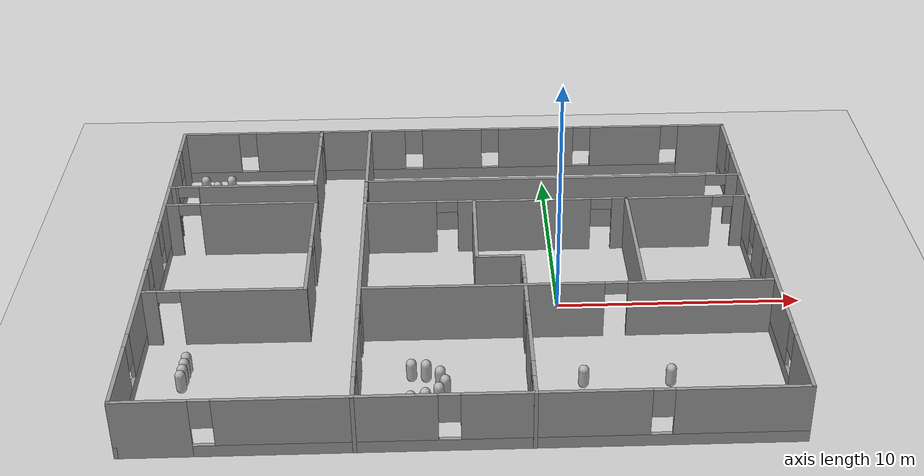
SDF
<sdf version='1.10'>
  <world name='default'>
    <plugin name='gz::sim::systems::Physics' filename='gz-sim-physics-system'/>
    <plugin name='gz::sim::systems::UserCommands' filename='gz-sim-user-commands-system'/>
    <plugin name='gz::sim::systems::SceneBroadcaster' filename='gz-sim-scene-broadcaster-system'/>
    <plugin name='gz::sim::systems::Sensors' filename='gz-sim-sensors-system'>
      <render_engine>ogre2</render_engine>
    </plugin>
    <plugin name='gz::sim::systems::Imu' filename='gz-sim-imu-system'/>
    <gui fullscreen='false'>
      <camera name='user_camera'>
        <pose>0.31965399999999999 -0.23500199999999999 9.2944099999999992 1.522609579747792e-17 1.5138000000000049 0.0095990000000000172</pose>
        <view_controller>orbit</view_controller>
        <projection_type>perspective</projection_type>
      </camera>
      <plugin name='3D View' filename='MinimalScene'>
        <gz-gui>
          <title>3D View</title>
          <property type='bool' key='showTitleBar'>false</property>
          <property type='string' key='state'>docked</property>
        </gz-gui>
        <engine>ogre2</engine>
        <scene>scene</scene>
        <ambient_light>0.4 0.4 0.4</ambient_light>
        <background_color>0.8 0.8 0.8</background_color>
        <camera_pose>0.319654 -0.235002 9.29441 0 1.5138 0.009599</camera_pose>
      </plugin>
      <plugin name='Entity context menu' filename='EntityContextMenuPlugin'>
        <gz-gui>
          <property key='state' type='string'>floating</property>
          <property key='width' type='double'>5</property>
          <property key='height' type='double'>5</property>
          <property key='showTitleBar' type='bool'>false</property>
        </gz-gui>
      </plugin>
      <plugin name='Scene Manager' filename='GzSceneManager'>
        <gz-gui>
          <property key='resizable' type='bool'>false</property>
          <property key='width' type='double'>5</property>
          <property key='height' type='double'>5</property>
          <property key='state' type='string'>floating</property>
          <property key='showTitleBar' type='bool'>false</property>
        </gz-gui>
      </plugin>
      <plugin name='Interactive view control' filename='InteractiveViewControl'>
        <gz-gui>
          <property key='resizable' type='bool'>false</property>
          <property key='width' type='double'>5</property>
          <property key='height' type='double'>5</property>
          <property key='state' type='string'>floating</property>
          <property key='showTitleBar' type='bool'>false</property>
        </gz-gui>
      </plugin>
      <plugin name='Camera Tracking' filename='CameraTracking'>
        <gz-gui>
          <property key='resizable' type='bool'>false</property>
          <property key='width' type='double'>5</property>
          <property key='height' type='double'>5</property>
          <property key='state' type='string'>floating</property>
          <property key='showTitleBar' type='bool'>false</property>
        </gz-gui>
      </plugin>
      <plugin name='Marker manager' filename='MarkerManager'>
        <gz-gui>
          <property key='resizable' type='bool'>false</property>
          <property key='width' type='double'>5</property>
          <property key='height' type='double'>5</property>
          <property key='state' type='string'>floating</property>
          <property key='showTitleBar' type='bool'>false</property>
        </gz-gui>
      </plugin>
      <plugin name='Select Entities' filename='SelectEntities'>
        <gz-gui>
          <property key='resizable' type='bool'>false</property>
          <property key='width' type='double'>5</property>
          <property key='height' type='double'>5</property>
          <property key='state' type='string'>floating</property>
          <property key='showTitleBar' type='bool'>false</property>
        </gz-gui>
      </plugin>
      <plugin name='Spawn Entities' filename='Spawn'>
        <gz-gui>
          <property key='resizable' type='bool'>false</property>
          <property key='width' type='double'>5</property>
          <property key='height' type='double'>5</property>
          <property key='state' type='string'>floating</property>
          <property key='showTitleBar' type='bool'>false</property>
        </gz-gui>
      </plugin>
      <plugin name='Visualization Capabilities' filename='VisualizationCapabilities'>
        <gz-gui>
          <property key='resizable' type='bool'>false</property>
          <property key='width' type='double'>5</property>
          <property key='height' type='double'>5</property>
          <property key='state' type='string'>floating</property>
          <property key='showTitleBar' type='bool'>false</property>
        </gz-gui>
      </plugin>
      <plugin name='World control' filename='WorldControl'>
        <gz-gui>
          <title>World control</title>
          <property type='bool' key='showTitleBar'>false</property>
          <property type='bool' key='resizable'>false</property>
          <property type='double' key='height'>72</property>
          <property type='double' key='z'>1</property>
          <property type='string' key='state'>floating</property>
          <anchors target='3D View'>
            <line own='left' target='left'/>
            <line own='bottom' target='bottom'/>
          </anchors>
        </gz-gui>
        <play_pause>true</play_pause>
        <step>true</step>
        <start_paused>true</start_paused>
        <use_event>true</use_event>
      </plugin>
      <plugin name='World stats' filename='WorldStats'>
        <gz-gui>
          <title>World stats</title>
          <property type='bool' key='showTitleBar'>false</property>
          <property type='bool' key='resizable'>false</property>
          <property type='double' key='height'>110</property>
          <property type='double' key='width'>290</property>
          <property type='double' key='z'>1</property>
          <property type='string' key='state'>floating</property>
          <anchors target='3D View'>
            <line own='right' target='right'/>
            <line own='bottom' target='bottom'/>
          </anchors>
        </gz-gui>
        <sim_time>true</sim_time>
        <real_time>true</real_time>
        <real_time_factor>true</real_time_factor>
        <iterations>true</iterations>
      </plugin>
      <plugin name='Shapes' filename='Shapes'>
        <gz-gui>
          <property key='resizable' type='bool'>false</property>
          <property key='x' type='double'>0</property>
          <property key='y' type='double'>0</property>
          <property key='width' type='double'>250</property>
          <property key='height' type='double'>50</property>
          <property key='state' type='string'>floating</property>
          <property key='showTitleBar' type='bool'>false</property>
          <property key='cardBackground' type='string'>#666666</property>
        </gz-gui>
      </plugin>
      <plugin name='Lights' filename='Lights'>
        <gz-gui>
          <property key='resizable' type='bool'>false</property>
          <property key='x' type='double'>250</property>
          <property key='y' type='double'>0</property>
          <property key='width' type='double'>150</property>
          <property key='height' type='double'>50</property>
          <property key='state' type='string'>floating</property>
          <property key='showTitleBar' type='bool'>false</property>
          <property key='cardBackground' type='string'>#666666</property>
        </gz-gui>
      </plugin>
      <plugin name='Transform control' filename='TransformControl'>
        <gz-gui>
          <property key='resizable' type='bool'>false</property>
          <property key='x' type='double'>0</property>
          <property key='y' type='double'>50</property>
          <property key='width' type='double'>250</property>
          <property key='height' type='double'>50</property>
          <property key='state' type='string'>floating</property>
          <property key='showTitleBar' type='bool'>false</property>
          <property key='cardBackground' type='string'>#777777</property>
        </gz-gui>
      </plugin>
      <plugin name='Screenshot' filename='Screenshot'>
        <gz-gui>
          <property key='resizable' type='bool'>false</property>
          <property key='x' type='double'>250</property>
          <property key='y' type='double'>50</property>
          <property key='width' type='double'>50</property>
          <property key='height' type='double'>50</property>
          <property key='state' type='string'>floating</property>
          <property key='showTitleBar' type='bool'>false</property>
          <property key='cardBackground' type='string'>#777777</property>
        </gz-gui>
      </plugin>
      <plugin name='CopyPaste' filename='CopyPaste'>
        <gz-gui>
          <property key='resizable' type='bool'>false</property>
          <property key='x' type='double'>300</property>
          <property key='y' type='double'>50</property>
          <property key='width' type='double'>100</property>
          <property key='height' type='double'>50</property>
          <property key='state' type='string'>floating</property>
          <property key='showTitleBar' type='bool'>false</property>
          <property key='cardBackground' type='string'>#777777</property>
        </gz-gui>
      </plugin>
      <plugin name='Component inspector' filename='ComponentInspector'>
        <gz-gui>
          <property type='bool' key='showTitleBar'>false</property>
          <property type='string' key='state'>docked</property>
        </gz-gui>
      </plugin>
      <plugin name='Entity tree' filename='EntityTree'>
        <gz-gui>
          <property type='bool' key='showTitleBar'>false</property>
          <property type='string' key='state'>docked</property>
        </gz-gui>
      </plugin>
    </gui>
    <physics type='ode'>
      <real_time_update_rate>1000</real_time_update_rate>
      <max_step_size>0.001</max_step_size>
      <real_time_factor>1</real_time_factor>
      <ode>
        <solver>
          <type>quick</type>
          <iters>150</iters>
          <precon_iters>0</precon_iters>
          <sor>1.3999999999999999</sor>
          <use_dynamic_moi_rescaling>true</use_dynamic_moi_rescaling>
        </solver>
        <constraints>
          <cfm>1.0000000000000001e-05</cfm>
          <erp>0.20000000000000001</erp>
          <contact_max_correcting_vel>2000</contact_max_correcting_vel>
          <contact_surface_layer>0.01</contact_surface_layer>
        </constraints>
      </ode>
    </physics>
    <gravity>0 0 -9.8000000000000007</gravity>
    <magnetic_field>5.5644999999999998e-06 2.2875799999999999e-05 -4.2388400000000002e-05</magnetic_field>
    <atmosphere type='adiabatic'/>
    <scene>
      <ambient>0.400000006 0.400000006 0.400000006 1</ambient>
      <background>0.699999988 0.699999988 0.699999988 1</background>
      <shadows>true</shadows>
    </scene>
    <include>
      <uri>https://fuel.gazebosim.org/1.0/OpenRobotics/models/Ground Plane</uri>
      <name>ground_plane</name>
      <pose>0 0 0 0 0 0</pose>
    </include>
    <model name='RoomWorld'>
      <pose>-4 1 0 0 0 0</pose>
      <link name='Wall_12'>
        <pose>-0.015924000000000001 -9.9163999999999994 0 0 0 0</pose>
        <visual name='Wall_12_Visual_0'>
          <pose>-11.0832 0 1.25 0 0 0</pose>
          <geometry>
            <box>
              <size>2.83352 0.14999999999999999 2.5</size>
            </box>
          </geometry>
          <material>
            <script>
              <uri>file://media/materials/scripts/gazebo.material</uri>
              <name>Gazebo/Grey</name>
            </script>
            <ambient>1 1 1 1</ambient>
          </material>
        </visual>
        <collision name='Wall_12_Collision_0'>
          <geometry>
            <box>
              <size>2.83352 0.14999999999999999 2.5</size>
            </box>
          </geometry>
          <pose>-11.0832 0 1.25 0 0 0</pose>
          <max_contacts>10</max_contacts>
          <surface>
            <bounce/>
            <friction>
              <ode/>
            </friction>
            <contact>
              <ode/>
            </contact>
          </surface>
        </collision>
        <visual name='Wall_12_Visual_1'>
          <pose>1.41676 0 0.25 0 0 0</pose>
          <geometry>
            <box>
              <size>22.166499999999999 0.14999999999999999 0.5</size>
            </box>
          </geometry>
          <material>
            <script>
              <uri>file://media/materials/scripts/gazebo.material</uri>
              <name>Gazebo/Grey</name>
            </script>
            <ambient>1 1 1 1</ambient>
          </material>
        </visual>
        <collision name='Wall_12_Collision_1'>
          <geometry>
            <box>
              <size>22.166499999999999 0.14999999999999999 0.5</size>
            </box>
          </geometry>
          <pose>1.41676 0 0.25 0 0 0</pose>
          <max_contacts>10</max_contacts>
          <surface>
            <bounce/>
            <friction>
              <ode/>
            </friction>
            <contact>
              <ode/>
            </contact>
          </surface>
        </collision>
        <visual name='Wall_12_Visual_2'>
          <pose>-4.8832300000000002 0 1.5 0 0 0</pose>
          <geometry>
            <box>
              <size>7.9664999999999999 0.14999999999999999 2</size>
            </box>
          </geometry>
          <material>
            <script>
              <uri>file://media/materials/scripts/gazebo.material</uri>
              <name>Gazebo/Grey</name>
            </script>
            <ambient>1 1 1 1</ambient>
          </material>
        </visual>
        <collision name='Wall_12_Collision_2'>
          <geometry>
            <box>
              <size>7.9664999999999999 0.14999999999999999 2</size>
            </box>
          </geometry>
          <pose>-4.8832300000000002 0 1.5 0 0 0</pose>
          <max_contacts>10</max_contacts>
          <surface>
            <bounce/>
            <friction>
              <ode/>
            </friction>
            <contact>
              <ode/>
            </contact>
          </surface>
        </collision>
        <visual name='Wall_12_Visual_3'>
          <pose>3.3050099999999998 0 1.5 0 0 0</pose>
          <geometry>
            <box>
              <size>6.8099699999999999 0.14999999999999999 2</size>
            </box>
          </geometry>
          <material>
            <script>
              <uri>file://media/materials/scripts/gazebo.material</uri>
              <name>Gazebo/Grey</name>
            </script>
            <ambient>1 1 1 1</ambient>
          </material>
        </visual>
        <collision name='Wall_12_Collision_3'>
          <geometry>
            <box>
              <size>6.8099699999999999 0.14999999999999999 2</size>
            </box>
          </geometry>
          <pose>3.3050099999999998 0 1.5 0 0 0</pose>
          <max_contacts>10</max_contacts>
          <surface>
            <bounce/>
            <friction>
              <ode/>
            </friction>
            <contact>
              <ode/>
            </contact>
          </surface>
        </collision>
        <visual name='Wall_12_Visual_4'>
          <pose>10.005000000000001 0 1.5 0 0 0</pose>
          <geometry>
            <box>
              <size>4.9900099999999998 0.14999999999999999 2</size>
            </box>
          </geometry>
          <material>
            <script>
              <uri>file://media/materials/scripts/gazebo.material</uri>
              <name>Gazebo/Grey</name>
            </script>
            <ambient>1 1 1 1</ambient>
          </material>
        </visual>
        <collision name='Wall_12_Collision_4'>
          <geometry>
            <box>
              <size>4.9900099999999998 0.14999999999999999 2</size>
            </box>
          </geometry>
          <pose>10.005000000000001 0 1.5 0 0 0</pose>
          <max_contacts>10</max_contacts>
          <surface>
            <bounce/>
            <friction>
              <ode/>
            </friction>
            <contact>
              <ode/>
            </contact>
          </surface>
        </collision>
        <visual name='Wall_12_Visual_5'>
          <pose>-9.2664799999999996 0 1.8999999999999999 0 0 0</pose>
          <geometry>
            <box>
              <size>0.80000000000000004 0.14999999999999999 1.2</size>
            </box>
          </geometry>
          <material>
            <script>
              <uri>file://media/materials/scripts/gazebo.material</uri>
              <name>Gazebo/Grey</name>
            </script>
            <ambient>1 1 1 1</ambient>
          </material>
        </visual>
        <collision name='Wall_12_Collision_5'>
          <geometry>
            <box>
              <size>0.80000000000000004 0.14999999999999999 1.2</size>
            </box>
          </geometry>
          <pose>-9.2664799999999996 0 1.8999999999999999 0 0 0</pose>
          <max_contacts>10</max_contacts>
          <surface>
            <bounce/>
            <friction>
              <ode/>
            </friction>
            <contact>
              <ode/>
            </contact>
          </surface>
        </collision>
        <visual name='Wall_12_Visual_6'>
          <pose>-0.49997799999999998 0 1.8999999999999999 0 0 0</pose>
          <geometry>
            <box>
              <size>0.80000000000000004 0.14999999999999999 1.2</size>
            </box>
          </geometry>
          <material>
            <script>
              <uri>file://media/materials/scripts/gazebo.material</uri>
              <name>Gazebo/Grey</name>
            </script>
            <ambient>1 1 1 1</ambient>
          </material>
        </visual>
        <collision name='Wall_12_Collision_6'>
          <geometry>
            <box>
              <size>0.80000000000000004 0.14999999999999999 1.2</size>
            </box>
          </geometry>
          <pose>-0.49997799999999998 0 1.8999999999999999 0 0 0</pose>
          <max_contacts>10</max_contacts>
          <surface>
            <bounce/>
            <friction>
              <ode/>
            </friction>
            <contact>
              <ode/>
            </contact>
          </surface>
        </collision>
        <visual name='Wall_12_Visual_7'>
          <pose>7.1099899999999998 0 1.8999999999999999 0 0 0</pose>
          <geometry>
            <box>
              <size>0.80000000000000004 0.14999999999999999 1.2</size>
            </box>
          </geometry>
          <material>
            <script>
              <uri>file://media/materials/scripts/gazebo.material</uri>
              <name>Gazebo/Grey</name>
            </script>
            <ambient>1 1 1 1</ambient>
          </material>
        </visual>
        <collision name='Wall_12_Collision_7'>
          <geometry>
            <box>
              <size>0.80000000000000004 0.14999999999999999 1.2</size>
            </box>
          </geometry>
          <pose>7.1099899999999998 0 1.8999999999999999 0 0 0</pose>
          <max_contacts>10</max_contacts>
          <surface>
            <bounce/>
            <friction>
              <ode/>
            </friction>
            <contact>
              <ode/>
            </contact>
          </surface>
        </collision>
        <velocity_decay>
          <linear>0</linear>
          <angular>0</angular>
        </velocity_decay>
        <self_collide>false</self_collide>
        <kinematic>false</kinematic>
        <gravity>true</gravity>
        <inertial>
          <pose>0 0 0 0 0 0</pose>
          <mass>1</mass>
          <inertia>
            <ixx>1</ixx>
            <ixy>0</ixy>
            <ixz>0</ixz>
            <iyy>1</iyy>
            <iyz>0</iyz>
            <izz>1</izz>
          </inertia>
        </inertial>
        <enable_wind>false</enable_wind>
      </link>
      <link name='Wall_13'>
        <pose>12.4091 0.008604000000000056 0 0 0 1.5708000000000006</pose>
        <visual name='Wall_13_Visual_0'>
          <pose>-8.4323200000000007 0 1.25 0 0 0</pose>
          <geometry>
            <box>
              <size>3.1353599999999999 0.14999999999999999 2.5</size>
            </box>
          </geometry>
          <material>
            <script>
              <uri>file://media/materials/scripts/gazebo.material</uri>
              <name>Gazebo/Grey</name>
            </script>
            <ambient>1 1 1 1</ambient>
          </material>
        </visual>
        <collision name='Wall_13_Collision_0'>
          <geometry>
            <box>
              <size>3.1353599999999999 0.14999999999999999 2.5</size>
            </box>
          </geometry>
          <pose>-8.4323200000000007 0 1.25 0 0 0</pose>
          <max_contacts>10</max_contacts>
          <surface>
            <bounce/>
            <friction>
              <ode/>
            </friction>
            <contact>
              <ode/>
            </contact>
          </surface>
        </collision>
        <visual name='Wall_13_Visual_1'>
          <pose>1.56768 0 0.25 0 0 0</pose>
          <geometry>
            <box>
              <size>16.864599999999999 0.14999999999999999 0.5</size>
            </box>
          </geometry>
          <material>
            <script>
              <uri>file://media/materials/scripts/gazebo.material</uri>
              <name>Gazebo/Grey</name>
            </script>
            <ambient>1 1 1 1</ambient>
          </material>
        </visual>
        <collision name='Wall_13_Collision_1'>
          <geometry>
            <box>
              <size>16.864599999999999 0.14999999999999999 0.5</size>
            </box>
          </geometry>
          <pose>1.56768 0 0.25 0 0 0</pose>
          <max_contacts>10</max_contacts>
          <surface>
            <bounce/>
            <friction>
              <ode/>
            </friction>
            <contact>
              <ode/>
            </contact>
          </surface>
        </collision>
        <visual name='Wall_13_Visual_2'>
          <pose>-3.8393199999999998 0 1.5 0 0 0</pose>
          <geometry>
            <box>
              <size>4.4506500000000004 0.14999999999999999 2</size>
            </box>
          </geometry>
          <material>
            <script>
              <uri>file://media/materials/scripts/gazebo.material</uri>
              <name>Gazebo/Grey</name>
            </script>
            <ambient>1 1 1 1</ambient>
          </material>
        </visual>
        <collision name='Wall_13_Collision_2'>
          <geometry>
            <box>
              <size>4.4506500000000004 0.14999999999999999 2</size>
            </box>
          </geometry>
          <pose>-3.8393199999999998 0 1.5 0 0 0</pose>
          <max_contacts>10</max_contacts>
          <surface>
            <bounce/>
            <friction>
              <ode/>
            </friction>
            <contact>
              <ode/>
            </contact>
          </surface>
        </collision>
        <visual name='Wall_13_Visual_3'>
          <pose>0.104448 0 1.5 0 0 0</pose>
          <geometry>
            <box>
              <size>1.8368899999999999 0.14999999999999999 2</size>
            </box>
          </geometry>
          <material>
            <script>
              <uri>file://media/materials/scripts/gazebo.material</uri>
              <name>Gazebo/Grey</name>
            </script>
            <ambient>1 1 1 1</ambient>
          </material>
        </visual>
        <collision name='Wall_13_Collision_3'>
          <geometry>
            <box>
              <size>1.8368899999999999 0.14999999999999999 2</size>
            </box>
          </geometry>
          <pose>0.104448 0 1.5 0 0 0</pose>
          <max_contacts>10</max_contacts>
          <surface>
            <bounce/>
            <friction>
              <ode/>
            </friction>
            <contact>
              <ode/>
            </contact>
          </surface>
        </collision>
        <visual name='Wall_13_Visual_4'>
          <pose>4.4992599999999996 0 1.5 0 0 0</pose>
          <geometry>
            <box>
              <size>5.3527399999999998 0.14999999999999999 2</size>
            </box>
          </geometry>
          <material>
            <script>
              <uri>file://media/materials/scripts/gazebo.material</uri>
              <name>Gazebo/Grey</name>
            </script>
            <ambient>1 1 1 1</ambient>
          </material>
        </visual>
        <collision name='Wall_13_Collision_4'>
          <geometry>
            <box>
              <size>5.3527399999999998 0.14999999999999999 2</size>
            </box>
          </geometry>
          <pose>4.4992599999999996 0 1.5 0 0 0</pose>
          <max_contacts>10</max_contacts>
          <surface>
            <bounce/>
            <friction>
              <ode/>
            </friction>
            <contact>
              <ode/>
            </contact>
          </surface>
        </collision>
        <visual name='Wall_13_Visual_5'>
          <pose>8.9878199999999993 0 1.5 0 0 0</pose>
          <geometry>
            <box>
              <size>2.0243699999999998 0.14999999999999999 2</size>
            </box>
          </geometry>
          <material>
            <script>
              <uri>file://media/materials/scripts/gazebo.material</uri>
              <name>Gazebo/Grey</name>
            </script>
            <ambient>1 1 1 1</ambient>
          </material>
        </visual>
        <collision name='Wall_13_Collision_5'>
          <geometry>
            <box>
              <size>2.0243699999999998 0.14999999999999999 2</size>
            </box>
          </geometry>
          <pose>8.9878199999999993 0 1.5 0 0 0</pose>
          <max_contacts>10</max_contacts>
          <surface>
            <bounce/>
            <friction>
              <ode/>
            </friction>
            <contact>
              <ode/>
            </contact>
          </surface>
        </collision>
        <visual name='Wall_13_Visual_6'>
          <pose>-6.4646400000000002 0 1.8999999999999999 0 0 0</pose>
          <geometry>
            <box>
              <size>0.80000000000000004 0.14999999999999999 1.2</size>
            </box>
          </geometry>
          <material>
            <script>
              <uri>file://media/materials/scripts/gazebo.material</uri>
              <name>Gazebo/Grey</name>
            </script>
            <ambient>1 1 1 1</ambient>
          </material>
        </visual>
        <collision name='Wall_13_Collision_6'>
          <geometry>
            <box>
              <size>0.80000000000000004 0.14999999999999999 1.2</size>
            </box>
          </geometry>
          <pose>-6.4646400000000002 0 1.8999999999999999 0 0 0</pose>
          <max_contacts>10</max_contacts>
          <surface>
            <bounce/>
            <friction>
              <ode/>
            </friction>
            <contact>
              <ode/>
            </contact>
          </surface>
        </collision>
        <visual name='Wall_13_Visual_7'>
          <pose>-1.214 0 1.8999999999999999 0 0 0</pose>
          <geometry>
            <box>
              <size>0.80000000000000004 0.14999999999999999 1.2</size>
            </box>
          </geometry>
          <material>
            <script>
              <uri>file://media/materials/scripts/gazebo.material</uri>
              <name>Gazebo/Grey</name>
            </script>
            <ambient>1 1 1 1</ambient>
          </material>
        </visual>
        <collision name='Wall_13_Collision_7'>
          <geometry>
            <box>
              <size>0.80000000000000004 0.14999999999999999 1.2</size>
            </box>
          </geometry>
          <pose>-1.214 0 1.8999999999999999 0 0 0</pose>
          <max_contacts>10</max_contacts>
          <surface>
            <bounce/>
            <friction>
              <ode/>
            </friction>
            <contact>
              <ode/>
            </contact>
          </surface>
        </collision>
        <visual name='Wall_13_Visual_8'>
          <pose>1.42289 0 1.8999999999999999 0 0 0</pose>
          <geometry>
            <box>
              <size>0.80000000000000004 0.14999999999999999 1.2</size>
            </box>
          </geometry>
          <material>
            <script>
              <uri>file://media/materials/scripts/gazebo.material</uri>
              <name>Gazebo/Grey</name>
            </script>
            <ambient>1 1 1 1</ambient>
          </material>
        </visual>
        <collision name='Wall_13_Collision_8'>
          <geometry>
            <box>
              <size>0.80000000000000004 0.14999999999999999 1.2</size>
            </box>
          </geometry>
          <pose>1.42289 0 1.8999999999999999 0 0 0</pose>
          <max_contacts>10</max_contacts>
          <surface>
            <bounce/>
            <friction>
              <ode/>
            </friction>
            <contact>
              <ode/>
            </contact>
          </surface>
        </collision>
        <visual name='Wall_13_Visual_9'>
          <pose>7.5756300000000003 0 1.8999999999999999 0 0 0</pose>
          <geometry>
            <box>
              <size>0.80000000000000004 0.14999999999999999 1.2</size>
            </box>
          </geometry>
          <material>
            <script>
              <uri>file://media/materials/scripts/gazebo.material</uri>
              <name>Gazebo/Grey</name>
            </script>
            <ambient>1 1 1 1</ambient>
          </material>
        </visual>
        <collision name='Wall_13_Collision_9'>
          <geometry>
            <box>
              <size>0.80000000000000004 0.14999999999999999 1.2</size>
            </box>
          </geometry>
          <pose>7.5756300000000003 0 1.8999999999999999 0 0 0</pose>
          <max_contacts>10</max_contacts>
          <surface>
            <bounce/>
            <friction>
              <ode/>
            </friction>
            <contact>
              <ode/>
            </contact>
          </surface>
        </collision>
        <velocity_decay>
          <linear>0</linear>
          <angular>0</angular>
        </velocity_decay>
        <self_collide>false</self_collide>
        <kinematic>false</kinematic>
        <gravity>true</gravity>
        <inertial>
          <pose>0 0 0 0 0 0</pose>
          <mass>1</mass>
          <inertia>
            <ixx>1</ixx>
            <ixy>0</ixy>
            <ixz>0</ixz>
            <iyy>1</iyy>
            <iyz>0</iyz>
            <izz>1</izz>
          </inertia>
        </inertial>
        <enable_wind>false</enable_wind>
      </link>
      <link name='Wall_14'>
        <pose>-0.015924000000000049 9.9336000000000002 0 0 0 3.1415899999999999</pose>
        <visual name='Wall_14_Visual_0'>
          <pose>-11.4391 0 1.25 0 0 0</pose>
          <geometry>
            <box>
              <size>2.12181 0.14999999999999999 2.5</size>
            </box>
          </geometry>
          <material>
            <script>
              <uri>file://media/materials/scripts/gazebo.material</uri>
              <name>Gazebo/Grey</name>
            </script>
            <ambient>1 1 1 1</ambient>
          </material>
        </visual>
        <collision name='Wall_14_Collision_0'>
          <geometry>
            <box>
              <size>2.12181 0.14999999999999999 2.5</size>
            </box>
          </geometry>
          <pose>-11.4391 0 1.25 0 0 0</pose>
          <max_contacts>10</max_contacts>
          <surface>
            <bounce/>
            <friction>
              <ode/>
            </friction>
            <contact>
              <ode/>
            </contact>
          </surface>
        </collision>
        <visual name='Wall_14_Visual_1'>
          <pose>1.06091 0 0.25 0 0 0</pose>
          <geometry>
            <box>
              <size>22.8782 0.14999999999999999 0.5</size>
            </box>
          </geometry>
          <material>
            <script>
              <uri>file://media/materials/scripts/gazebo.material</uri>
              <name>Gazebo/Grey</name>
            </script>
            <ambient>1 1 1 1</ambient>
          </material>
        </visual>
        <collision name='Wall_14_Collision_1'>
          <geometry>
            <box>
              <size>22.8782 0.14999999999999999 0.5</size>
            </box>
          </geometry>
          <pose>1.06091 0 0.25 0 0 0</pose>
          <max_contacts>10</max_contacts>
          <surface>
            <bounce/>
            <friction>
              <ode/>
            </friction>
            <contact>
              <ode/>
            </contact>
          </surface>
        </collision>
        <visual name='Wall_14_Visual_2'>
          <pose>-7.9311299999999996 0 1.5 0 0 0</pose>
          <geometry>
            <box>
              <size>3.2941199999999999 0.14999999999999999 2</size>
            </box>
          </geometry>
          <material>
            <script>
              <uri>file://media/materials/scripts/gazebo.material</uri>
              <name>Gazebo/Grey</name>
            </script>
            <ambient>1 1 1 1</ambient>
          </material>
        </visual>
        <collision name='Wall_14_Collision_2'>
          <geometry>
            <box>
              <size>3.2941199999999999 0.14999999999999999 2</size>
            </box>
          </geometry>
          <pose>-7.9311299999999996 0 1.5 0 0 0</pose>
          <max_contacts>10</max_contacts>
          <surface>
            <bounce/>
            <friction>
              <ode/>
            </friction>
            <contact>
              <ode/>
            </contact>
          </surface>
        </collision>
        <visual name='Wall_14_Visual_3'>
          <pose>-3.7560500000000001 0 1.5 0 0 0</pose>
          <geometry>
            <box>
              <size>3.4560300000000002 0.14999999999999999 2</size>
            </box>
          </geometry>
          <material>
            <script>
              <uri>file://media/materials/scripts/gazebo.material</uri>
              <name>Gazebo/Grey</name>
            </script>
            <ambient>1 1 1 1</ambient>
          </material>
        </visual>
        <collision name='Wall_14_Collision_3'>
          <geometry>
            <box>
              <size>3.4560300000000002 0.14999999999999999 2</size>
            </box>
          </geometry>
          <pose>-3.7560500000000001 0 1.5 0 0 0</pose>
          <max_contacts>10</max_contacts>
          <surface>
            <bounce/>
            <friction>
              <ode/>
            </friction>
            <contact>
              <ode/>
            </contact>
          </surface>
        </collision>
        <visual name='Wall_14_Visual_4'>
          <pose>0.141454 0 1.5 0 0 0</pose>
          <geometry>
            <box>
              <size>2.7389800000000002 0.14999999999999999 2</size>
            </box>
          </geometry>
          <material>
            <script>
              <uri>file://media/materials/scripts/gazebo.material</uri>
              <name>Gazebo/Grey</name>
            </script>
            <ambient>1 1 1 1</ambient>
          </material>
        </visual>
        <collision name='Wall_14_Collision_4'>
          <geometry>
            <box>
              <size>2.7389800000000002 0.14999999999999999 2</size>
            </box>
          </geometry>
          <pose>0.141454 0 1.5 0 0 0</pose>
          <max_contacts>10</max_contacts>
          <surface>
            <bounce/>
            <friction>
              <ode/>
            </friction>
            <contact>
              <ode/>
            </contact>
          </surface>
        </collision>
        <visual name='Wall_14_Visual_5'>
          <pose>5.7390600000000003 0 1.5 0 0 0</pose>
          <geometry>
            <box>
              <size>6.85623 0.14999999999999999 2</size>
            </box>
          </geometry>
          <material>
            <script>
              <uri>file://media/materials/scripts/gazebo.material</uri>
              <name>Gazebo/Grey</name>
            </script>
            <ambient>1 1 1 1</ambient>
          </material>
        </visual>
        <collision name='Wall_14_Collision_5'>
          <geometry>
            <box>
              <size>6.85623 0.14999999999999999 2</size>
            </box>
          </geometry>
          <pose>5.7390600000000003 0 1.5 0 0 0</pose>
          <max_contacts>10</max_contacts>
          <surface>
            <bounce/>
            <friction>
              <ode/>
            </friction>
            <contact>
              <ode/>
            </contact>
          </surface>
        </collision>
        <visual name='Wall_14_Visual_6'>
          <pose>11.233599999999999 0 1.5 0 0 0</pose>
          <geometry>
            <box>
              <size>2.5328200000000001 0.14999999999999999 2</size>
            </box>
          </geometry>
          <material>
            <script>
              <uri>file://media/materials/scripts/gazebo.material</uri>
              <name>Gazebo/Grey</name>
            </script>
            <ambient>1 1 1 1</ambient>
          </material>
        </visual>
        <collision name='Wall_14_Collision_6'>
          <geometry>
            <box>
              <size>2.5328200000000001 0.14999999999999999 2</size>
            </box>
          </geometry>
          <pose>11.233599999999999 0 1.5 0 0 0</pose>
          <max_contacts>10</max_contacts>
          <surface>
            <bounce/>
            <friction>
              <ode/>
            </friction>
            <contact>
              <ode/>
            </contact>
          </surface>
        </collision>
        <visual name='Wall_14_Visual_7'>
          <pose>-9.9781899999999997 0 1.8999999999999999 0 0 0</pose>
          <geometry>
            <box>
              <size>0.80000000000000004 0.14999999999999999 1.2</size>
            </box>
          </geometry>
          <material>
            <script>
              <uri>file://media/materials/scripts/gazebo.material</uri>
              <name>Gazebo/Grey</name>
            </script>
            <ambient>1 1 1 1</ambient>
          </material>
        </visual>
        <collision name='Wall_14_Collision_7'>
          <geometry>
            <box>
              <size>0.80000000000000004 0.14999999999999999 1.2</size>
            </box>
          </geometry>
          <pose>-9.9781899999999997 0 1.8999999999999999 0 0 0</pose>
          <max_contacts>10</max_contacts>
          <surface>
            <bounce/>
            <friction>
              <ode/>
            </friction>
            <contact>
              <ode/>
            </contact>
          </surface>
        </collision>
        <visual name='Wall_14_Visual_8'>
          <pose>-5.8840700000000004 0 1.8999999999999999 0 0 0</pose>
          <geometry>
            <box>
              <size>0.80000000000000004 0.14999999999999999 1.2</size>
            </box>
          </geometry>
          <material>
            <script>
              <uri>file://media/materials/scripts/gazebo.material</uri>
              <name>Gazebo/Grey</name>
            </script>
            <ambient>1 1 1 1</ambient>
          </material>
        </visual>
        <collision name='Wall_14_Collision_8'>
          <geometry>
            <box>
              <size>0.80000000000000004 0.14999999999999999 1.2</size>
            </box>
          </geometry>
          <pose>-5.8840700000000004 0 1.8999999999999999 0 0 0</pose>
          <max_contacts>10</max_contacts>
          <surface>
            <bounce/>
            <friction>
              <ode/>
            </friction>
            <contact>
              <ode/>
            </contact>
          </surface>
        </collision>
        <visual name='Wall_14_Visual_9'>
          <pose>-1.6280399999999999 0 1.8999999999999999 0 0 0</pose>
          <geometry>
            <box>
              <size>0.80000000000000004 0.14999999999999999 1.2</size>
            </box>
          </geometry>
          <material>
            <script>
              <uri>file://media/materials/scripts/gazebo.material</uri>
              <name>Gazebo/Grey</name>
            </script>
            <ambient>1 1 1 1</ambient>
          </material>
        </visual>
        <collision name='Wall_14_Collision_9'>
          <geometry>
            <box>
              <size>0.80000000000000004 0.14999999999999999 1.2</size>
            </box>
          </geometry>
          <pose>-1.6280399999999999 0 1.8999999999999999 0 0 0</pose>
          <max_contacts>10</max_contacts>
          <surface>
            <bounce/>
            <friction>
              <ode/>
            </friction>
            <contact>
              <ode/>
            </contact>
          </surface>
        </collision>
        <visual name='Wall_14_Visual_10'>
          <pose>1.9109400000000001 0 1.8999999999999999 0 0 0</pose>
          <geometry>
            <box>
              <size>0.80000000000000004 0.14999999999999999 1.2</size>
            </box>
          </geometry>
          <material>
            <script>
              <uri>file://media/materials/scripts/gazebo.material</uri>
              <name>Gazebo/Grey</name>
            </script>
            <ambient>1 1 1 1</ambient>
          </material>
        </visual>
        <collision name='Wall_14_Collision_10'>
          <geometry>
            <box>
              <size>0.80000000000000004 0.14999999999999999 1.2</size>
            </box>
          </geometry>
          <pose>1.9109400000000001 0 1.8999999999999999 0 0 0</pose>
          <max_contacts>10</max_contacts>
          <surface>
            <bounce/>
            <friction>
              <ode/>
            </friction>
            <contact>
              <ode/>
            </contact>
          </surface>
        </collision>
        <visual name='Wall_14_Visual_11'>
          <pose>9.5671800000000005 0 1.8999999999999999 0 0 0</pose>
          <geometry>
            <box>
              <size>0.80000000000000004 0.14999999999999999 1.2</size>
            </box>
          </geometry>
          <material>
            <script>
              <uri>file://media/materials/scripts/gazebo.material</uri>
              <name>Gazebo/Grey</name>
            </script>
            <ambient>1 1 1 1</ambient>
          </material>
        </visual>
        <collision name='Wall_14_Collision_11'>
          <geometry>
            <box>
              <size>0.80000000000000004 0.14999999999999999 1.2</size>
            </box>
          </geometry>
          <pose>9.5671800000000005 0 1.8999999999999999 0 0 0</pose>
          <max_contacts>10</max_contacts>
          <surface>
            <bounce/>
            <friction>
              <ode/>
            </friction>
            <contact>
              <ode/>
            </contact>
          </surface>
        </collision>
        <velocity_decay>
          <linear>0</linear>
          <angular>0</angular>
        </velocity_decay>
        <self_collide>false</self_collide>
        <kinematic>false</kinematic>
        <gravity>true</gravity>
        <inertial>
          <pose>0 0 0 0 0 0</pose>
          <mass>1</mass>
          <inertia>
            <ixx>1</ixx>
            <ixy>0</ixy>
            <ixz>0</ixz>
            <iyy>1</iyy>
            <iyz>0</iyz>
            <izz>1</izz>
          </inertia>
        </inertial>
        <enable_wind>false</enable_wind>
      </link>
      <link name='Wall_15'>
        <pose>-12.440899999999999 0.008604000000000056 0 0 0 -1.5708000000000006</pose>
        <visual name='Wall_15_Visual_0'>
          <pose>-9.1497299999999999 0 1.25 0 0 0</pose>
          <geometry>
            <box>
              <size>1.7005399999999999 0.14999999999999999 2.5</size>
            </box>
          </geometry>
          <material>
            <script>
              <uri>file://media/materials/scripts/gazebo.material</uri>
              <name>Gazebo/Grey</name>
            </script>
            <ambient>1 1 1 1</ambient>
          </material>
        </visual>
        <collision name='Wall_15_Collision_0'>
          <geometry>
            <box>
              <size>1.7005399999999999 0.14999999999999999 2.5</size>
            </box>
          </geometry>
          <pose>-9.1497299999999999 0 1.25 0 0 0</pose>
          <max_contacts>10</max_contacts>
          <surface>
            <bounce/>
            <friction>
              <ode/>
            </friction>
            <contact>
              <ode/>
            </contact>
          </surface>
        </collision>
        <visual name='Wall_15_Visual_1'>
          <pose>0.85026900000000005 0 0.25 0 0 0</pose>
          <geometry>
            <box>
              <size>18.299499999999998 0.14999999999999999 0.5</size>
            </box>
          </geometry>
          <material>
            <script>
              <uri>file://media/materials/scripts/gazebo.material</uri>
              <name>Gazebo/Grey</name>
            </script>
            <ambient>1 1 1 1</ambient>
          </material>
        </visual>
        <collision name='Wall_15_Collision_1'>
          <geometry>
            <box>
              <size>18.299499999999998 0.14999999999999999 0.5</size>
            </box>
          </geometry>
          <pose>0.85026900000000005 0 0.25 0 0 0</pose>
          <max_contacts>10</max_contacts>
          <surface>
            <bounce/>
            <friction>
              <ode/>
            </friction>
            <contact>
              <ode/>
            </contact>
          </surface>
        </collision>
        <visual name='Wall_15_Visual_2'>
          <pose>-4.8115300000000003 0 1.5 0 0 0</pose>
          <geometry>
            <box>
              <size>5.3758699999999999 0.14999999999999999 2</size>
            </box>
          </geometry>
          <material>
            <script>
              <uri>file://media/materials/scripts/gazebo.material</uri>
              <name>Gazebo/Grey</name>
            </script>
            <ambient>1 1 1 1</ambient>
          </material>
        </visual>
        <collision name='Wall_15_Collision_2'>
          <geometry>
            <box>
              <size>5.3758699999999999 0.14999999999999999 2</size>
            </box>
          </geometry>
          <pose>-4.8115300000000003 0 1.5 0 0 0</pose>
          <max_contacts>10</max_contacts>
          <surface>
            <bounce/>
            <friction>
              <ode/>
            </friction>
            <contact>
              <ode/>
            </contact>
          </surface>
        </collision>
        <visual name='Wall_15_Visual_3'>
          <pose>-0.31262299999999998 0 1.5 0 0 0</pose>
          <geometry>
            <box>
              <size>2.0219299999999998 0.14999999999999999 2</size>
            </box>
          </geometry>
          <material>
            <script>
              <uri>file://media/materials/scripts/gazebo.material</uri>
              <name>Gazebo/Grey</name>
            </script>
            <ambient>1 1 1 1</ambient>
          </material>
        </visual>
        <collision name='Wall_15_Collision_3'>
          <geometry>
            <box>
              <size>2.0219299999999998 0.14999999999999999 2</size>
            </box>
          </geometry>
          <pose>-0.31262299999999998 0 1.5 0 0 0</pose>
          <max_contacts>10</max_contacts>
          <surface>
            <bounce/>
            <friction>
              <ode/>
            </friction>
            <contact>
              <ode/>
            </contact>
          </surface>
        </collision>
        <visual name='Wall_15_Visual_4'>
          <pose>3.6774100000000001 0 1.5 0 0 0</pose>
          <geometry>
            <box>
              <size>4.3581300000000001 0.14999999999999999 2</size>
            </box>
          </geometry>
          <material>
            <script>
              <uri>file://media/materials/scripts/gazebo.material</uri>
              <name>Gazebo/Grey</name>
            </script>
            <ambient>1 1 1 1</ambient>
          </material>
        </visual>
        <collision name='Wall_15_Collision_4'>
          <geometry>
            <box>
              <size>4.3581300000000001 0.14999999999999999 2</size>
            </box>
          </geometry>
          <pose>3.6774100000000001 0 1.5 0 0 0</pose>
          <max_contacts>10</max_contacts>
          <surface>
            <bounce/>
            <friction>
              <ode/>
            </friction>
            <contact>
              <ode/>
            </contact>
          </surface>
        </collision>
        <visual name='Wall_15_Visual_5'>
          <pose>8.3282299999999996 0 1.5 0 0 0</pose>
          <geometry>
            <box>
              <size>3.3435299999999999 0.14999999999999999 2</size>
            </box>
          </geometry>
          <material>
            <script>
              <uri>file://media/materials/scripts/gazebo.material</uri>
              <name>Gazebo/Grey</name>
            </script>
            <ambient>1 1 1 1</ambient>
          </material>
        </visual>
        <collision name='Wall_15_Collision_5'>
          <geometry>
            <box>
              <size>3.3435299999999999 0.14999999999999999 2</size>
            </box>
          </geometry>
          <pose>8.3282299999999996 0 1.5 0 0 0</pose>
          <max_contacts>10</max_contacts>
          <surface>
            <bounce/>
            <friction>
              <ode/>
            </friction>
            <contact>
              <ode/>
            </contact>
          </surface>
        </collision>
        <visual name='Wall_15_Visual_6'>
          <pose>-7.8994600000000004 0 1.8999999999999999 0 0 0</pose>
          <geometry>
            <box>
              <size>0.80000000000000004 0.14999999999999999 1.2</size>
            </box>
          </geometry>
          <material>
            <script>
              <uri>file://media/materials/scripts/gazebo.material</uri>
              <name>Gazebo/Grey</name>
            </script>
            <ambient>1 1 1 1</ambient>
          </material>
        </visual>
        <collision name='Wall_15_Collision_6'>
          <geometry>
            <box>
              <size>0.80000000000000004 0.14999999999999999 1.2</size>
            </box>
          </geometry>
          <pose>-7.8994600000000004 0 1.8999999999999999 0 0 0</pose>
          <max_contacts>10</max_contacts>
          <surface>
            <bounce/>
            <friction>
              <ode/>
            </friction>
            <contact>
              <ode/>
            </contact>
          </surface>
        </collision>
        <visual name='Wall_15_Visual_7'>
          <pose>-1.72359 0 1.8999999999999999 0 0 0</pose>
          <geometry>
            <box>
              <size>0.80000000000000004 0.14999999999999999 1.2</size>
            </box>
          </geometry>
          <material>
            <script>
              <uri>file://media/materials/scripts/gazebo.material</uri>
              <name>Gazebo/Grey</name>
            </script>
            <ambient>1 1 1 1</ambient>
          </material>
        </visual>
        <collision name='Wall_15_Collision_7'>
          <geometry>
            <box>
              <size>0.80000000000000004 0.14999999999999999 1.2</size>
            </box>
          </geometry>
          <pose>-1.72359 0 1.8999999999999999 0 0 0</pose>
          <max_contacts>10</max_contacts>
          <surface>
            <bounce/>
            <friction>
              <ode/>
            </friction>
            <contact>
              <ode/>
            </contact>
          </surface>
        </collision>
        <visual name='Wall_15_Visual_8'>
          <pose>1.0983400000000001 0 1.8999999999999999 0 0 0</pose>
          <geometry>
            <box>
              <size>0.80000000000000004 0.14999999999999999 1.2</size>
            </box>
          </geometry>
          <material>
            <script>
              <uri>file://media/materials/scripts/gazebo.material</uri>
              <name>Gazebo/Grey</name>
            </script>
            <ambient>1 1 1 1</ambient>
          </material>
        </visual>
        <collision name='Wall_15_Collision_8'>
          <geometry>
            <box>
              <size>0.80000000000000004 0.14999999999999999 1.2</size>
            </box>
          </geometry>
          <pose>1.0983400000000001 0 1.8999999999999999 0 0 0</pose>
          <max_contacts>10</max_contacts>
          <surface>
            <bounce/>
            <friction>
              <ode/>
            </friction>
            <contact>
              <ode/>
            </contact>
          </surface>
        </collision>
        <visual name='Wall_15_Visual_9'>
          <pose>6.2564700000000002 0 1.8999999999999999 0 0 0</pose>
          <geometry>
            <box>
              <size>0.80000000000000004 0.14999999999999999 1.2</size>
            </box>
          </geometry>
          <material>
            <script>
              <uri>file://media/materials/scripts/gazebo.material</uri>
              <name>Gazebo/Grey</name>
            </script>
            <ambient>1 1 1 1</ambient>
          </material>
        </visual>
        <collision name='Wall_15_Collision_9'>
          <geometry>
            <box>
              <size>0.80000000000000004 0.14999999999999999 1.2</size>
            </box>
          </geometry>
          <pose>6.2564700000000002 0 1.8999999999999999 0 0 0</pose>
          <max_contacts>10</max_contacts>
          <surface>
            <bounce/>
            <friction>
              <ode/>
            </friction>
            <contact>
              <ode/>
            </contact>
          </surface>
        </collision>
        <velocity_decay>
          <linear>0</linear>
          <angular>0</angular>
        </velocity_decay>
        <self_collide>false</self_collide>
        <kinematic>false</kinematic>
        <gravity>true</gravity>
        <inertial>
          <pose>0 0 0 0 0 0</pose>
          <mass>1</mass>
          <inertia>
            <ixx>1</ixx>
            <ixy>0</ixy>
            <ixz>0</ixz>
            <iyy>1</iyy>
            <iyz>0</iyz>
            <izz>1</izz>
          </inertia>
        </inertial>
        <enable_wind>false</enable_wind>
      </link>
      <link name='Wall_17'>
        <pose>-9.2054100000000005 3.5661100000000001 0 0 0 0</pose>
        <visual name='Wall_17_Visual_0'>
          <pose>-2.9429599999999998 0 1.25 0 0 0</pose>
          <geometry>
            <box>
              <size>0.61408399999999996 0.14999999999999999 2.5</size>
            </box>
          </geometry>
          <material>
            <script>
              <uri>file://media/materials/scripts/gazebo.material</uri>
              <name>Gazebo/Grey</name>
            </script>
            <ambient>1 1 1 1</ambient>
          </material>
        </visual>
        <collision name='Wall_17_Collision_0'>
          <geometry>
            <box>
              <size>0.61408399999999996 0.14999999999999999 2.5</size>
            </box>
          </geometry>
          <pose>-2.9429599999999998 0 1.25 0 0 0</pose>
          <max_contacts>10</max_contacts>
          <surface>
            <bounce/>
            <friction>
              <ode/>
            </friction>
            <contact>
              <ode/>
            </contact>
          </surface>
        </collision>
        <visual name='Wall_17_Visual_1'>
          <pose>0.75704199999999999 0 1.25 0 0 0</pose>
          <geometry>
            <box>
              <size>4.9859200000000001 0.14999999999999999 2.5</size>
            </box>
          </geometry>
          <material>
            <script>
              <uri>file://media/materials/scripts/gazebo.material</uri>
              <name>Gazebo/Grey</name>
            </script>
            <ambient>1 1 1 1</ambient>
          </material>
        </visual>
        <collision name='Wall_17_Collision_1'>
          <geometry>
            <box>
              <size>4.9859200000000001 0.14999999999999999 2.5</size>
            </box>
          </geometry>
          <pose>0.75704199999999999 0 1.25 0 0 0</pose>
          <max_contacts>10</max_contacts>
          <surface>
            <bounce/>
            <friction>
              <ode/>
            </friction>
            <contact>
              <ode/>
            </contact>
          </surface>
        </collision>
        <visual name='Wall_17_Visual_2'>
          <pose>-2.1859199999999999 0 2.25 0 0 0</pose>
          <geometry>
            <box>
              <size>0.90000000000000002 0.14999999999999999 0.5</size>
            </box>
          </geometry>
          <material>
            <script>
              <uri>file://media/materials/scripts/gazebo.material</uri>
              <name>Gazebo/Grey</name>
            </script>
            <ambient>1 1 1 1</ambient>
          </material>
        </visual>
        <collision name='Wall_17_Collision_2'>
          <geometry>
            <box>
              <size>0.90000000000000002 0.14999999999999999 0.5</size>
            </box>
          </geometry>
          <pose>-2.1859199999999999 0 2.25 0 0 0</pose>
          <max_contacts>10</max_contacts>
          <surface>
            <bounce/>
            <friction>
              <ode/>
            </friction>
            <contact>
              <ode/>
            </contact>
          </surface>
        </collision>
        <velocity_decay>
          <linear>0</linear>
          <angular>0</angular>
        </velocity_decay>
        <self_collide>false</self_collide>
        <kinematic>false</kinematic>
        <gravity>true</gravity>
        <inertial>
          <pose>0 0 0 0 0 0</pose>
          <mass>1</mass>
          <inertia>
            <ixx>1</ixx>
            <ixy>0</ixy>
            <ixz>0</ixz>
            <iyy>1</iyy>
            <iyz>0</iyz>
            <izz>1</izz>
          </inertia>
        </inertial>
        <enable_wind>false</enable_wind>
      </link>
      <link name='Wall_18'>
        <pose>-6.0304099999999998 0.26611200000000013 0 0 0 -1.5708000000000006</pose>
        <visual name='Wall_18_Visual_0'>
          <pose>-1.9943500000000001 0 1.25 0 0 0</pose>
          <geometry>
            <box>
              <size>2.7612999999999999 0.14999999999999999 2.5</size>
            </box>
          </geometry>
          <material>
            <script>
              <uri>file://media/materials/scripts/gazebo.material</uri>
              <name>Gazebo/Grey</name>
            </script>
            <ambient>1 1 1 1</ambient>
          </material>
        </visual>
        <collision name='Wall_18_Collision_0'>
          <geometry>
            <box>
              <size>2.7612999999999999 0.14999999999999999 2.5</size>
            </box>
          </geometry>
          <pose>-1.9943500000000001 0 1.25 0 0 0</pose>
          <max_contacts>10</max_contacts>
          <surface>
            <bounce/>
            <friction>
              <ode/>
            </friction>
            <contact>
              <ode/>
            </contact>
          </surface>
        </collision>
        <visual name='Wall_18_Visual_1'>
          <pose>1.8306500000000001 0 1.25 0 0 0</pose>
          <geometry>
            <box>
              <size>3.0886999999999998 0.14999999999999999 2.5</size>
            </box>
          </geometry>
          <material>
            <script>
              <uri>file://media/materials/scripts/gazebo.material</uri>
              <name>Gazebo/Grey</name>
            </script>
            <ambient>1 1 1 1</ambient>
          </material>
        </visual>
        <collision name='Wall_18_Collision_1'>
          <geometry>
            <box>
              <size>3.0886999999999998 0.14999999999999999 2.5</size>
            </box>
          </geometry>
          <pose>1.8306500000000001 0 1.25 0 0 0</pose>
          <max_contacts>10</max_contacts>
          <surface>
            <bounce/>
            <friction>
              <ode/>
            </friction>
            <contact>
              <ode/>
            </contact>
          </surface>
        </collision>
        <visual name='Wall_18_Visual_2'>
          <pose>-0.16370299999999999 0 2.25 0 0 0</pose>
          <geometry>
            <box>
              <size>0.90000000000000002 0.14999999999999999 0.5</size>
            </box>
          </geometry>
          <material>
            <script>
              <uri>file://media/materials/scripts/gazebo.material</uri>
              <name>Gazebo/Grey</name>
            </script>
            <ambient>1 1 1 1</ambient>
          </material>
        </visual>
        <collision name='Wall_18_Collision_2'>
          <geometry>
            <box>
              <size>0.90000000000000002 0.14999999999999999 0.5</size>
            </box>
          </geometry>
          <pose>-0.16370299999999999 0 2.25 0 0 0</pose>
          <max_contacts>10</max_contacts>
          <surface>
            <bounce/>
            <friction>
              <ode/>
            </friction>
            <contact>
              <ode/>
            </contact>
          </surface>
        </collision>
        <velocity_decay>
          <linear>0</linear>
          <angular>0</angular>
        </velocity_decay>
        <self_collide>false</self_collide>
        <kinematic>false</kinematic>
        <gravity>true</gravity>
        <inertial>
          <pose>0 0 0 0 0 0</pose>
          <mass>1</mass>
          <inertia>
            <ixx>1</ixx>
            <ixy>0</ixy>
            <ixz>0</ixz>
            <iyy>1</iyy>
            <iyz>0</iyz>
            <izz>1</izz>
          </inertia>
        </inertial>
        <enable_wind>false</enable_wind>
      </link>
      <link name='Wall_19'>
        <pose>-9.2054100000000005 -3.03389 0 0 0 3.1415899999999999</pose>
        <visual name='Wall_19_Visual_0'>
          <pose>-0.78721200000000002 0 1.25 0 0 0</pose>
          <geometry>
            <box>
              <size>4.9255800000000001 0.14999999999999999 2.5</size>
            </box>
          </geometry>
          <material>
            <script>
              <uri>file://media/materials/scripts/gazebo.material</uri>
              <name>Gazebo/Grey</name>
            </script>
            <ambient>1 1 1 1</ambient>
          </material>
        </visual>
        <collision name='Wall_19_Collision_0'>
          <geometry>
            <box>
              <size>4.9255800000000001 0.14999999999999999 2.5</size>
            </box>
          </geometry>
          <pose>-0.78721200000000002 0 1.25 0 0 0</pose>
          <max_contacts>10</max_contacts>
          <surface>
            <bounce/>
            <friction>
              <ode/>
            </friction>
            <contact>
              <ode/>
            </contact>
          </surface>
        </collision>
        <visual name='Wall_19_Visual_1'>
          <pose>2.9127900000000002 0 1.25 0 0 0</pose>
          <geometry>
            <box>
              <size>0.67442500000000005 0.14999999999999999 2.5</size>
            </box>
          </geometry>
          <material>
            <script>
              <uri>file://media/materials/scripts/gazebo.material</uri>
              <name>Gazebo/Grey</name>
            </script>
            <ambient>1 1 1 1</ambient>
          </material>
        </visual>
        <collision name='Wall_19_Collision_1'>
          <geometry>
            <box>
              <size>0.67442500000000005 0.14999999999999999 2.5</size>
            </box>
          </geometry>
          <pose>2.9127900000000002 0 1.25 0 0 0</pose>
          <max_contacts>10</max_contacts>
          <surface>
            <bounce/>
            <friction>
              <ode/>
            </friction>
            <contact>
              <ode/>
            </contact>
          </surface>
        </collision>
        <visual name='Wall_19_Visual_2'>
          <pose>2.1255700000000002 0 2.25 0 0 0</pose>
          <geometry>
            <box>
              <size>0.90000000000000002 0.14999999999999999 0.5</size>
            </box>
          </geometry>
          <material>
            <script>
              <uri>file://media/materials/scripts/gazebo.material</uri>
              <name>Gazebo/Grey</name>
            </script>
            <ambient>1 1 1 1</ambient>
          </material>
        </visual>
        <collision name='Wall_19_Collision_2'>
          <geometry>
            <box>
              <size>0.90000000000000002 0.14999999999999999 0.5</size>
            </box>
          </geometry>
          <pose>2.1255700000000002 0 2.25 0 0 0</pose>
          <max_contacts>10</max_contacts>
          <surface>
            <bounce/>
            <friction>
              <ode/>
            </friction>
            <contact>
              <ode/>
            </contact>
          </surface>
        </collision>
        <velocity_decay>
          <linear>0</linear>
          <angular>0</angular>
        </velocity_decay>
        <self_collide>false</self_collide>
        <kinematic>false</kinematic>
        <gravity>true</gravity>
        <inertial>
          <pose>0 0 0 0 0 0</pose>
          <mass>1</mass>
          <inertia>
            <ixx>1</ixx>
            <ixy>0</ixy>
            <ixz>0</ixz>
            <iyy>1</iyy>
            <iyz>0</iyz>
            <izz>1</izz>
          </inertia>
        </inertial>
        <enable_wind>false</enable_wind>
      </link>
      <link name='Wall_21'>
        <pose>-6.1582699999999999 7.5020300000000013 0 0 0 -1.5708000000000006</pose>
        <visual name='Wall_21_Visual_0'>
          <pose>-2.2230799999999999 0 1.25 0 0 0</pose>
          <geometry>
            <box>
              <size>0.55383199999999999 0.14999999999999999 2.5</size>
            </box>
          </geometry>
          <material>
            <script>
              <uri>file://media/materials/scripts/gazebo.material</uri>
              <name>Gazebo/Grey</name>
            </script>
            <ambient>1 1 1 1</ambient>
          </material>
        </visual>
        <collision name='Wall_21_Collision_0'>
          <geometry>
            <box>
              <size>0.55383199999999999 0.14999999999999999 2.5</size>
            </box>
          </geometry>
          <pose>-2.2230799999999999 0 1.25 0 0 0</pose>
          <max_contacts>10</max_contacts>
          <surface>
            <bounce/>
            <friction>
              <ode/>
            </friction>
            <contact>
              <ode/>
            </contact>
          </surface>
        </collision>
        <visual name='Wall_21_Visual_1'>
          <pose>0.72691600000000001 0 1.25 0 0 0</pose>
          <geometry>
            <box>
              <size>3.54617 0.14999999999999999 2.5</size>
            </box>
          </geometry>
          <material>
            <script>
              <uri>file://media/materials/scripts/gazebo.material</uri>
              <name>Gazebo/Grey</name>
            </script>
            <ambient>1 1 1 1</ambient>
          </material>
        </visual>
        <collision name='Wall_21_Collision_1'>
          <geometry>
            <box>
              <size>3.54617 0.14999999999999999 2.5</size>
            </box>
          </geometry>
          <pose>0.72691600000000001 0 1.25 0 0 0</pose>
          <max_contacts>10</max_contacts>
          <surface>
            <bounce/>
            <friction>
              <ode/>
            </friction>
            <contact>
              <ode/>
            </contact>
          </surface>
        </collision>
        <visual name='Wall_21_Visual_2'>
          <pose>-1.49617 0 2.25 0 0 0</pose>
          <geometry>
            <box>
              <size>0.90000000000000002 0.14999999999999999 0.5</size>
            </box>
          </geometry>
          <material>
            <script>
              <uri>file://media/materials/scripts/gazebo.material</uri>
              <name>Gazebo/Grey</name>
            </script>
            <ambient>1 1 1 1</ambient>
          </material>
        </visual>
        <collision name='Wall_21_Collision_2'>
          <geometry>
            <box>
              <size>0.90000000000000002 0.14999999999999999 0.5</size>
            </box>
          </geometry>
          <pose>-1.49617 0 2.25 0 0 0</pose>
          <max_contacts>10</max_contacts>
          <surface>
            <bounce/>
            <friction>
              <ode/>
            </friction>
            <contact>
              <ode/>
            </contact>
          </surface>
        </collision>
        <velocity_decay>
          <linear>0</linear>
          <angular>0</angular>
        </velocity_decay>
        <self_collide>false</self_collide>
        <kinematic>false</kinematic>
        <gravity>true</gravity>
        <inertial>
          <pose>0 0 0 0 0 0</pose>
          <mass>1</mass>
          <inertia>
            <ixx>1</ixx>
            <ixy>0</ixy>
            <ixz>0</ixz>
            <iyy>1</iyy>
            <iyz>0</iyz>
            <izz>1</izz>
          </inertia>
        </inertial>
        <enable_wind>false</enable_wind>
      </link>
      <link name='Wall_22'>
        <pose>-9.2082800000000002 5.0770299999999997 0 0 0 3.1415899999999999</pose>
        <visual name='Wall_22_Visual_0'>
          <pose>-0.57529399999999997 0 1.25 0 0 0</pose>
          <geometry>
            <box>
              <size>5.0994099999999998 0.14999999999999999 2.5</size>
            </box>
          </geometry>
          <material>
            <script>
              <uri>file://media/materials/scripts/gazebo.material</uri>
              <name>Gazebo/Grey</name>
            </script>
            <ambient>1 1 1 1</ambient>
          </material>
        </visual>
        <collision name='Wall_22_Collision_0'>
          <geometry>
            <box>
              <size>5.0994099999999998 0.14999999999999999 2.5</size>
            </box>
          </geometry>
          <pose>-0.57529399999999997 0 1.25 0 0 0</pose>
          <max_contacts>10</max_contacts>
          <surface>
            <bounce/>
            <friction>
              <ode/>
            </friction>
            <contact>
              <ode/>
            </contact>
          </surface>
        </collision>
        <visual name='Wall_22_Visual_1'>
          <pose>2.9997099999999999 0 1.25 0 0 0</pose>
          <geometry>
            <box>
              <size>0.25058799999999998 0.14999999999999999 2.5</size>
            </box>
          </geometry>
          <material>
            <script>
              <uri>file://media/materials/scripts/gazebo.material</uri>
              <name>Gazebo/Grey</name>
            </script>
            <ambient>1 1 1 1</ambient>
          </material>
        </visual>
        <collision name='Wall_22_Collision_1'>
          <geometry>
            <box>
              <size>0.25058799999999998 0.14999999999999999 2.5</size>
            </box>
          </geometry>
          <pose>2.9997099999999999 0 1.25 0 0 0</pose>
          <max_contacts>10</max_contacts>
          <surface>
            <bounce/>
            <friction>
              <ode/>
            </friction>
            <contact>
              <ode/>
            </contact>
          </surface>
        </collision>
        <visual name='Wall_22_Visual_2'>
          <pose>2.42441 0 2.25 0 0 0</pose>
          <geometry>
            <box>
              <size>0.90000000000000002 0.14999999999999999 0.5</size>
            </box>
          </geometry>
          <material>
            <script>
              <uri>file://media/materials/scripts/gazebo.material</uri>
              <name>Gazebo/Grey</name>
            </script>
            <ambient>1 1 1 1</ambient>
          </material>
        </visual>
        <collision name='Wall_22_Collision_2'>
          <geometry>
            <box>
              <size>0.90000000000000002 0.14999999999999999 0.5</size>
            </box>
          </geometry>
          <pose>2.42441 0 2.25 0 0 0</pose>
          <max_contacts>10</max_contacts>
          <surface>
            <bounce/>
            <friction>
              <ode/>
            </friction>
            <contact>
              <ode/>
            </contact>
          </surface>
        </collision>
        <velocity_decay>
          <linear>0</linear>
          <angular>0</angular>
        </velocity_decay>
        <self_collide>false</self_collide>
        <kinematic>false</kinematic>
        <gravity>true</gravity>
        <inertial>
          <pose>0 0 0 0 0 0</pose>
          <mass>1</mass>
          <inertia>
            <ixx>1</ixx>
            <ixy>0</ixy>
            <ixz>0</ixz>
            <iyy>1</iyy>
            <iyz>0</iyz>
            <izz>1</izz>
          </inertia>
        </inertial>
        <enable_wind>false</enable_wind>
      </link>
      <link name='Wall_24'>
        <collision name='Wall_24_Collision'>
          <geometry>
            <box>
              <size>0.25 0.14999999999999999 2.5</size>
            </box>
          </geometry>
          <pose>0 0 1.25 0 0 0</pose>
          <max_contacts>10</max_contacts>
          <surface>
            <bounce/>
            <friction>
              <ode/>
            </friction>
            <contact>
              <ode/>
            </contact>
          </surface>
        </collision>
        <visual name='Wall_24_Visual'>
          <pose>0 0 1.25 0 0 0</pose>
          <geometry>
            <box>
              <size>0.25 0.14999999999999999 2.5</size>
            </box>
          </geometry>
          <material>
            <script>
              <uri>file://media/materials/scripts/gazebo.material</uri>
              <name>Gazebo/Grey</name>
            </script>
            <ambient>1 1 1 1</ambient>
          </material>
        </visual>
        <pose>-12.308299999999999 5.0770299999999997 0 0 0 3.1415899999999999</pose>
        <velocity_decay>
          <linear>0</linear>
          <angular>0</angular>
        </velocity_decay>
        <self_collide>false</self_collide>
        <kinematic>false</kinematic>
        <gravity>true</gravity>
        <inertial>
          <pose>0 0 0 0 0 0</pose>
          <mass>1</mass>
          <inertia>
            <ixx>1</ixx>
            <ixy>0</ixy>
            <ixz>0</ixz>
            <iyy>1</iyy>
            <iyz>0</iyz>
            <izz>1</izz>
          </inertia>
        </inertial>
        <enable_wind>false</enable_wind>
      </link>
      <link name='Wall_28'>
        <pose>-3.9378799999999998 -0.0069360000000000532 0 0 0 -1.5708000000000006</pose>
        <visual name='Wall_28_Visual_0'>
          <pose>-7.3943899999999996 0 1.25 0 0 0</pose>
          <geometry>
            <box>
              <size>5.21122 0.14999999999999999 2.5</size>
            </box>
          </geometry>
          <material>
            <script>
              <uri>file://media/materials/scripts/gazebo.material</uri>
              <name>Gazebo/Grey</name>
            </script>
            <ambient>1 1 1 1</ambient>
          </material>
        </visual>
        <collision name='Wall_28_Collision_0'>
          <geometry>
            <box>
              <size>5.21122 0.14999999999999999 2.5</size>
            </box>
          </geometry>
          <pose>-7.3943899999999996 0 1.25 0 0 0</pose>
          <max_contacts>10</max_contacts>
          <surface>
            <bounce/>
            <friction>
              <ode/>
            </friction>
            <contact>
              <ode/>
            </contact>
          </surface>
        </collision>
        <visual name='Wall_28_Visual_1'>
          <pose>0.17671200000000001 0 1.25 0 0 0</pose>
          <geometry>
            <box>
              <size>8.1309900000000006 0.14999999999999999 2.5</size>
            </box>
          </geometry>
          <material>
            <script>
              <uri>file://media/materials/scripts/gazebo.material</uri>
              <name>Gazebo/Grey</name>
            </script>
            <ambient>1 1 1 1</ambient>
          </material>
        </visual>
        <collision name='Wall_28_Collision_1'>
          <geometry>
            <box>
              <size>8.1309900000000006 0.14999999999999999 2.5</size>
            </box>
          </geometry>
          <pose>0.17671200000000001 0 1.25 0 0 0</pose>
          <max_contacts>10</max_contacts>
          <surface>
            <bounce/>
            <friction>
              <ode/>
            </friction>
            <contact>
              <ode/>
            </contact>
          </surface>
        </collision>
        <visual name='Wall_28_Visual_2'>
          <pose>6.5024300000000004 0 1.25 0 0 0</pose>
          <geometry>
            <box>
              <size>2.72044 0.14999999999999999 2.5</size>
            </box>
          </geometry>
          <material>
            <script>
              <uri>file://media/materials/scripts/gazebo.material</uri>
              <name>Gazebo/Grey</name>
            </script>
            <ambient>1 1 1 1</ambient>
          </material>
        </visual>
        <collision name='Wall_28_Collision_2'>
          <geometry>
            <box>
              <size>2.72044 0.14999999999999999 2.5</size>
            </box>
          </geometry>
          <pose>6.5024300000000004 0 1.25 0 0 0</pose>
          <max_contacts>10</max_contacts>
          <surface>
            <bounce/>
            <friction>
              <ode/>
            </friction>
            <contact>
              <ode/>
            </contact>
          </surface>
        </collision>
        <visual name='Wall_28_Visual_3'>
          <pose>9.3813300000000002 0 1.25 0 0 0</pose>
          <geometry>
            <box>
              <size>1.2373499999999999 0.14999999999999999 2.5</size>
            </box>
          </geometry>
          <material>
            <script>
              <uri>file://media/materials/scripts/gazebo.material</uri>
              <name>Gazebo/Grey</name>
            </script>
            <ambient>1 1 1 1</ambient>
          </material>
        </visual>
        <collision name='Wall_28_Collision_3'>
          <geometry>
            <box>
              <size>1.2373499999999999 0.14999999999999999 2.5</size>
            </box>
          </geometry>
          <pose>9.3813300000000002 0 1.25 0 0 0</pose>
          <max_contacts>10</max_contacts>
          <surface>
            <bounce/>
            <friction>
              <ode/>
            </friction>
            <contact>
              <ode/>
            </contact>
          </surface>
        </collision>
        <visual name='Wall_28_Visual_4'>
          <pose>-4.3387799999999999 0 2.25 0 0 0</pose>
          <geometry>
            <box>
              <size>0.90000000000000002 0.14999999999999999 0.5</size>
            </box>
          </geometry>
          <material>
            <script>
              <uri>file://media/materials/scripts/gazebo.material</uri>
              <name>Gazebo/Grey</name>
            </script>
            <ambient>1 1 1 1</ambient>
          </material>
        </visual>
        <collision name='Wall_28_Collision_4'>
          <geometry>
            <box>
              <size>0.90000000000000002 0.14999999999999999 0.5</size>
            </box>
          </geometry>
          <pose>-4.3387799999999999 0 2.25 0 0 0</pose>
          <max_contacts>10</max_contacts>
          <surface>
            <bounce/>
            <friction>
              <ode/>
            </friction>
            <contact>
              <ode/>
            </contact>
          </surface>
        </collision>
        <visual name='Wall_28_Visual_5'>
          <pose>4.6922100000000002 0 2.25 0 0 0</pose>
          <geometry>
            <box>
              <size>0.90000000000000002 0.14999999999999999 0.5</size>
            </box>
          </geometry>
          <material>
            <script>
              <uri>file://media/materials/scripts/gazebo.material</uri>
              <name>Gazebo/Grey</name>
            </script>
            <ambient>1 1 1 1</ambient>
          </material>
        </visual>
        <collision name='Wall_28_Collision_5'>
          <geometry>
            <box>
              <size>0.90000000000000002 0.14999999999999999 0.5</size>
            </box>
          </geometry>
          <pose>4.6922100000000002 0 2.25 0 0 0</pose>
          <max_contacts>10</max_contacts>
          <surface>
            <bounce/>
            <friction>
              <ode/>
            </friction>
            <contact>
              <ode/>
            </contact>
          </surface>
        </collision>
        <visual name='Wall_28_Visual_6'>
          <pose>8.3126499999999997 0 2.25 0 0 0</pose>
          <geometry>
            <box>
              <size>0.90000000000000002 0.14999999999999999 0.5</size>
            </box>
          </geometry>
          <material>
            <script>
              <uri>file://media/materials/scripts/gazebo.material</uri>
              <name>Gazebo/Grey</name>
            </script>
            <ambient>1 1 1 1</ambient>
          </material>
        </visual>
        <collision name='Wall_28_Collision_6'>
          <geometry>
            <box>
              <size>0.90000000000000002 0.14999999999999999 0.5</size>
            </box>
          </geometry>
          <pose>8.3126499999999997 0 2.25 0 0 0</pose>
          <max_contacts>10</max_contacts>
          <surface>
            <bounce/>
            <friction>
              <ode/>
            </friction>
            <contact>
              <ode/>
            </contact>
          </surface>
        </collision>
        <velocity_decay>
          <linear>0</linear>
          <angular>0</angular>
        </velocity_decay>
        <self_collide>false</self_collide>
        <kinematic>false</kinematic>
        <gravity>true</gravity>
        <inertial>
          <pose>0 0 0 0 0 0</pose>
          <mass>1</mass>
          <inertia>
            <ixx>1</ixx>
            <ixy>0</ixy>
            <ixz>0</ixz>
            <iyy>1</iyy>
            <iyz>0</iyz>
            <izz>1</izz>
          </inertia>
        </inertial>
        <enable_wind>false</enable_wind>
      </link>
      <link name='Wall_30'>
        <pose>4.2458099999999996 5.2570699999999997 0 0 0 0</pose>
        <visual name='Wall_30_Visual_0'>
          <pose>-0.78428600000000004 0 1.25 0 0 0</pose>
          <geometry>
            <box>
              <size>14.9314 0.14999999999999999 2.5</size>
            </box>
          </geometry>
          <material>
            <script>
              <uri>file://media/materials/scripts/gazebo.material</uri>
              <name>Gazebo/Grey</name>
            </script>
            <ambient>1 1 1 1</ambient>
          </material>
        </visual>
        <collision name='Wall_30_Collision_0'>
          <geometry>
            <box>
              <size>14.9314 0.14999999999999999 2.5</size>
            </box>
          </geometry>
          <pose>-0.78428600000000004 0 1.25 0 0 0</pose>
          <max_contacts>10</max_contacts>
          <surface>
            <bounce/>
            <friction>
              <ode/>
            </friction>
            <contact>
              <ode/>
            </contact>
          </surface>
        </collision>
        <visual name='Wall_30_Visual_1'>
          <pose>7.9157099999999998 0 1.25 0 0 0</pose>
          <geometry>
            <box>
              <size>0.66857100000000003 0.14999999999999999 2.5</size>
            </box>
          </geometry>
          <material>
            <script>
              <uri>file://media/materials/scripts/gazebo.material</uri>
              <name>Gazebo/Grey</name>
            </script>
            <ambient>1 1 1 1</ambient>
          </material>
        </visual>
        <collision name='Wall_30_Collision_1'>
          <geometry>
            <box>
              <size>0.66857100000000003 0.14999999999999999 2.5</size>
            </box>
          </geometry>
          <pose>7.9157099999999998 0 1.25 0 0 0</pose>
          <max_contacts>10</max_contacts>
          <surface>
            <bounce/>
            <friction>
              <ode/>
            </friction>
            <contact>
              <ode/>
            </contact>
          </surface>
        </collision>
        <visual name='Wall_30_Visual_2'>
          <pose>7.1314299999999999 0 2.25 0 0 0</pose>
          <geometry>
            <box>
              <size>0.90000000000000002 0.14999999999999999 0.5</size>
            </box>
          </geometry>
          <material>
            <script>
              <uri>file://media/materials/scripts/gazebo.material</uri>
              <name>Gazebo/Grey</name>
            </script>
            <ambient>1 1 1 1</ambient>
          </material>
        </visual>
        <collision name='Wall_30_Collision_2'>
          <geometry>
            <box>
              <size>0.90000000000000002 0.14999999999999999 0.5</size>
            </box>
          </geometry>
          <pose>7.1314299999999999 0 2.25 0 0 0</pose>
          <max_contacts>10</max_contacts>
          <surface>
            <bounce/>
            <friction>
              <ode/>
            </friction>
            <contact>
              <ode/>
            </contact>
          </surface>
        </collision>
        <velocity_decay>
          <linear>0</linear>
          <angular>0</angular>
        </velocity_decay>
        <self_collide>false</self_collide>
        <kinematic>false</kinematic>
        <gravity>true</gravity>
        <inertial>
          <pose>0 0 0 0 0 0</pose>
          <mass>1</mass>
          <inertia>
            <ixx>1</ixx>
            <ixy>0</ixy>
            <ixz>0</ixz>
            <iyy>1</iyy>
            <iyz>0</iyz>
            <izz>1</izz>
          </inertia>
        </inertial>
        <enable_wind>false</enable_wind>
      </link>
      <link name='Wall_32'>
        <pose>4.26593 3.4066200000000002 0 0 0 0</pose>
        <visual name='Wall_32_Visual_0'>
          <pose>-6.7077299999999997 0 1.25 0 0 0</pose>
          <geometry>
            <box>
              <size>3.08453 0.14999999999999999 2.5</size>
            </box>
          </geometry>
          <material>
            <script>
              <uri>file://media/materials/scripts/gazebo.material</uri>
              <name>Gazebo/Grey</name>
            </script>
            <ambient>1 1 1 1</ambient>
          </material>
        </visual>
        <collision name='Wall_32_Collision_0'>
          <geometry>
            <box>
              <size>3.08453 0.14999999999999999 2.5</size>
            </box>
          </geometry>
          <pose>-6.7077299999999997 0 1.25 0 0 0</pose>
          <max_contacts>10</max_contacts>
          <surface>
            <bounce/>
            <friction>
              <ode/>
            </friction>
            <contact>
              <ode/>
            </contact>
          </surface>
        </collision>
        <visual name='Wall_32_Visual_1'>
          <pose>-1.4168400000000001 0 1.25 0 0 0</pose>
          <geometry>
            <box>
              <size>5.6972500000000004 0.14999999999999999 2.5</size>
            </box>
          </geometry>
          <material>
            <script>
              <uri>file://media/materials/scripts/gazebo.material</uri>
              <name>Gazebo/Grey</name>
            </script>
            <ambient>1 1 1 1</ambient>
          </material>
        </visual>
        <collision name='Wall_32_Collision_1'>
          <geometry>
            <box>
              <size>5.6972500000000004 0.14999999999999999 2.5</size>
            </box>
          </geometry>
          <pose>-1.4168400000000001 0 1.25 0 0 0</pose>
          <max_contacts>10</max_contacts>
          <surface>
            <bounce/>
            <friction>
              <ode/>
            </friction>
            <contact>
              <ode/>
            </contact>
          </surface>
        </collision>
        <visual name='Wall_32_Visual_2'>
          <pose>4.49655 0 1.25 0 0 0</pose>
          <geometry>
            <box>
              <size>4.3295300000000001 0.14999999999999999 2.5</size>
            </box>
          </geometry>
          <material>
            <script>
              <uri>file://media/materials/scripts/gazebo.material</uri>
              <name>Gazebo/Grey</name>
            </script>
            <ambient>1 1 1 1</ambient>
          </material>
        </visual>
        <collision name='Wall_32_Collision_2'>
          <geometry>
            <box>
              <size>4.3295300000000001 0.14999999999999999 2.5</size>
            </box>
          </geometry>
          <pose>4.49655 0 1.25 0 0 0</pose>
          <max_contacts>10</max_contacts>
          <surface>
            <bounce/>
            <friction>
              <ode/>
            </friction>
            <contact>
              <ode/>
            </contact>
          </surface>
        </collision>
        <visual name='Wall_32_Visual_3'>
          <pose>7.9056600000000001 0 1.25 0 0 0</pose>
          <geometry>
            <box>
              <size>0.68868499999999999 0.14999999999999999 2.5</size>
            </box>
          </geometry>
          <material>
            <script>
              <uri>file://media/materials/scripts/gazebo.material</uri>
              <name>Gazebo/Grey</name>
            </script>
            <ambient>1 1 1 1</ambient>
          </material>
        </visual>
        <collision name='Wall_32_Collision_3'>
          <geometry>
            <box>
              <size>0.68868499999999999 0.14999999999999999 2.5</size>
            </box>
          </geometry>
          <pose>7.9056600000000001 0 1.25 0 0 0</pose>
          <max_contacts>10</max_contacts>
          <surface>
            <bounce/>
            <friction>
              <ode/>
            </friction>
            <contact>
              <ode/>
            </contact>
          </surface>
        </collision>
        <visual name='Wall_32_Visual_4'>
          <pose>-4.7154699999999998 0 2.25 0 0 0</pose>
          <geometry>
            <box>
              <size>0.90000000000000002 0.14999999999999999 0.5</size>
            </box>
          </geometry>
          <material>
            <script>
              <uri>file://media/materials/scripts/gazebo.material</uri>
              <name>Gazebo/Grey</name>
            </script>
            <ambient>1 1 1 1</ambient>
          </material>
        </visual>
        <collision name='Wall_32_Collision_4'>
          <geometry>
            <box>
              <size>0.90000000000000002 0.14999999999999999 0.5</size>
            </box>
          </geometry>
          <pose>-4.7154699999999998 0 2.25 0 0 0</pose>
          <max_contacts>10</max_contacts>
          <surface>
            <bounce/>
            <friction>
              <ode/>
            </friction>
            <contact>
              <ode/>
            </contact>
          </surface>
        </collision>
        <visual name='Wall_32_Visual_5'>
          <pose>1.8817900000000001 0 2.25 0 0 0</pose>
          <geometry>
            <box>
              <size>0.90000000000000002 0.14999999999999999 0.5</size>
            </box>
          </geometry>
          <material>
            <script>
              <uri>file://media/materials/scripts/gazebo.material</uri>
              <name>Gazebo/Grey</name>
            </script>
            <ambient>1 1 1 1</ambient>
          </material>
        </visual>
        <collision name='Wall_32_Collision_5'>
          <geometry>
            <box>
              <size>0.90000000000000002 0.14999999999999999 0.5</size>
            </box>
          </geometry>
          <pose>1.8817900000000001 0 2.25 0 0 0</pose>
          <max_contacts>10</max_contacts>
          <surface>
            <bounce/>
            <friction>
              <ode/>
            </friction>
            <contact>
              <ode/>
            </contact>
          </surface>
        </collision>
        <visual name='Wall_32_Visual_6'>
          <pose>7.1113200000000001 0 2.25 0 0 0</pose>
          <geometry>
            <box>
              <size>0.90000000000000002 0.14999999999999999 0.5</size>
            </box>
          </geometry>
          <material>
            <script>
              <uri>file://media/materials/scripts/gazebo.material</uri>
              <name>Gazebo/Grey</name>
            </script>
            <ambient>1 1 1 1</ambient>
          </material>
        </visual>
        <collision name='Wall_32_Collision_6'>
          <geometry>
            <box>
              <size>0.90000000000000002 0.14999999999999999 0.5</size>
            </box>
          </geometry>
          <pose>7.1113200000000001 0 2.25 0 0 0</pose>
          <max_contacts>10</max_contacts>
          <surface>
            <bounce/>
            <friction>
              <ode/>
            </friction>
            <contact>
              <ode/>
            </contact>
          </surface>
        </collision>
        <velocity_decay>
          <linear>0</linear>
          <angular>0</angular>
        </velocity_decay>
        <self_collide>false</self_collide>
        <kinematic>false</kinematic>
        <gravity>true</gravity>
        <inertial>
          <pose>0 0 0 0 0 0</pose>
          <mass>1</mass>
          <inertia>
            <ixx>1</ixx>
            <ixy>0</ixy>
            <ixz>0</ixz>
            <iyy>1</iyy>
            <iyz>0</iyz>
            <izz>1</izz>
          </inertia>
        </inertial>
        <enable_wind>false</enable_wind>
      </link>
      <link name='Wall_34'>
        <pose>4.2012700000000001 -3.0900599999999998 0 0 0 0</pose>
        <visual name='Wall_34_Visual_0'>
          <pose>-3.33439 0 1.25 0 0 0</pose>
          <geometry>
            <box>
              <size>9.5812200000000001 0.14999999999999999 2.5</size>
            </box>
          </geometry>
          <material>
            <script>
              <uri>file://media/materials/scripts/gazebo.material</uri>
              <name>Gazebo/Grey</name>
            </script>
            <ambient>1 1 1 1</ambient>
          </material>
        </visual>
        <collision name='Wall_34_Collision_0'>
          <geometry>
            <box>
              <size>9.5812200000000001 0.14999999999999999 2.5</size>
            </box>
          </geometry>
          <pose>-3.33439 0 1.25 0 0 0</pose>
          <max_contacts>10</max_contacts>
          <surface>
            <bounce/>
            <friction>
              <ode/>
            </friction>
            <contact>
              <ode/>
            </contact>
          </surface>
        </collision>
        <visual name='Wall_34_Visual_1'>
          <pose>5.2406100000000002 0 1.25 0 0 0</pose>
          <geometry>
            <box>
              <size>5.7687799999999996 0.14999999999999999 2.5</size>
            </box>
          </geometry>
          <material>
            <script>
              <uri>file://media/materials/scripts/gazebo.material</uri>
              <name>Gazebo/Grey</name>
            </script>
            <ambient>1 1 1 1</ambient>
          </material>
        </visual>
        <collision name='Wall_34_Collision_1'>
          <geometry>
            <box>
              <size>5.7687799999999996 0.14999999999999999 2.5</size>
            </box>
          </geometry>
          <pose>5.2406100000000002 0 1.25 0 0 0</pose>
          <max_contacts>10</max_contacts>
          <surface>
            <bounce/>
            <friction>
              <ode/>
            </friction>
            <contact>
              <ode/>
            </contact>
          </surface>
        </collision>
        <visual name='Wall_34_Visual_2'>
          <pose>1.90622 0 2.25 0 0 0</pose>
          <geometry>
            <box>
              <size>0.90000000000000002 0.14999999999999999 0.5</size>
            </box>
          </geometry>
          <material>
            <script>
              <uri>file://media/materials/scripts/gazebo.material</uri>
              <name>Gazebo/Grey</name>
            </script>
            <ambient>1 1 1 1</ambient>
          </material>
        </visual>
        <collision name='Wall_34_Collision_2'>
          <geometry>
            <box>
              <size>0.90000000000000002 0.14999999999999999 0.5</size>
            </box>
          </geometry>
          <pose>1.90622 0 2.25 0 0 0</pose>
          <max_contacts>10</max_contacts>
          <surface>
            <bounce/>
            <friction>
              <ode/>
            </friction>
            <contact>
              <ode/>
            </contact>
          </surface>
        </collision>
        <velocity_decay>
          <linear>0</linear>
          <angular>0</angular>
        </velocity_decay>
        <self_collide>false</self_collide>
        <kinematic>false</kinematic>
        <gravity>true</gravity>
        <inertial>
          <pose>0 0 0 0 0 0</pose>
          <mass>1</mass>
          <inertia>
            <ixx>1</ixx>
            <ixy>0</ixy>
            <ixz>0</ixz>
            <iyy>1</iyy>
            <iyz>0</iyz>
            <izz>1</izz>
          </inertia>
        </inertial>
        <enable_wind>false</enable_wind>
      </link>
      <link name='Wall_36'>
        <collision name='Wall_36_Collision'>
          <geometry>
            <box>
              <size>4.5 0.14999999999999999 2.5</size>
            </box>
          </geometry>
          <pose>0 0 1.25 0 0 0</pose>
          <max_contacts>10</max_contacts>
          <surface>
            <bounce/>
            <friction>
              <ode/>
            </friction>
            <contact>
              <ode/>
            </contact>
          </surface>
        </collision>
        <visual name='Wall_36_Visual'>
          <pose>0 0 1.25 0 0 0</pose>
          <geometry>
            <box>
              <size>4.5 0.14999999999999999 2.5</size>
            </box>
          </geometry>
          <material>
            <script>
              <uri>file://media/materials/scripts/gazebo.material</uri>
              <name>Gazebo/Grey</name>
            </script>
            <ambient>1 1 1 1</ambient>
          </material>
        </visual>
        <pose>0.69693300000000002 1.1913999999999998 0 0 0 -1.5708000000000006</pose>
        <velocity_decay>
          <linear>0</linear>
          <angular>0</angular>
        </velocity_decay>
        <self_collide>false</self_collide>
        <kinematic>false</kinematic>
        <gravity>true</gravity>
        <inertial>
          <pose>0 0 0 0 0 0</pose>
          <mass>1</mass>
          <inertia>
            <ixx>1</ixx>
            <ixy>0</ixy>
            <ixz>0</ixz>
            <iyy>1</iyy>
            <iyz>0</iyz>
            <izz>1</izz>
          </inertia>
        </inertial>
        <enable_wind>false</enable_wind>
      </link>
      <link name='Wall_37'>
        <collision name='Wall_37_Collision'>
          <geometry>
            <box>
              <size>2 0.14999999999999999 2.5</size>
            </box>
          </geometry>
          <pose>0 0 1.25 0 0 0</pose>
          <max_contacts>10</max_contacts>
          <surface>
            <bounce/>
            <friction>
              <ode/>
            </friction>
            <contact>
              <ode/>
            </contact>
          </surface>
        </collision>
        <visual name='Wall_37_Visual'>
          <pose>0 0 1.25 0 0 0</pose>
          <geometry>
            <box>
              <size>2 0.14999999999999999 2.5</size>
            </box>
          </geometry>
          <material>
            <script>
              <uri>file://media/materials/scripts/gazebo.material</uri>
              <name>Gazebo/Grey</name>
            </script>
            <ambient>1 1 1 1</ambient>
          </material>
        </visual>
        <pose>1.6219299999999999 -0.98360300000000001 0 0 0 0</pose>
        <velocity_decay>
          <linear>0</linear>
          <angular>0</angular>
        </velocity_decay>
        <self_collide>false</self_collide>
        <kinematic>false</kinematic>
        <gravity>true</gravity>
        <inertial>
          <pose>0 0 0 0 0 0</pose>
          <mass>1</mass>
          <inertia>
            <ixx>1</ixx>
            <ixy>0</ixy>
            <ixz>0</ixz>
            <iyy>1</iyy>
            <iyz>0</iyz>
            <izz>1</izz>
          </inertia>
        </inertial>
        <enable_wind>false</enable_wind>
      </link>
      <link name='Wall_38'>
        <pose>2.5469300000000001 -2.0335999999999999 0 0 0 -1.5708000000000006</pose>
        <visual name='Wall_38_Visual_0'>
          <pose>-0.74199700000000002 0 1.25 0 0 0</pose>
          <geometry>
            <box>
              <size>0.76600500000000005 0.14999999999999999 2.5</size>
            </box>
          </geometry>
          <material>
            <script>
              <uri>file://media/materials/scripts/gazebo.material</uri>
              <name>Gazebo/Grey</name>
            </script>
            <ambient>1 1 1 1</ambient>
          </material>
        </visual>
        <collision name='Wall_38_Collision_0'>
          <geometry>
            <box>
              <size>0.76600500000000005 0.14999999999999999 2.5</size>
            </box>
          </geometry>
          <pose>-0.74199700000000002 0 1.25 0 0 0</pose>
          <max_contacts>10</max_contacts>
          <surface>
            <bounce/>
            <friction>
              <ode/>
            </friction>
            <contact>
              <ode/>
            </contact>
          </surface>
        </collision>
        <visual name='Wall_38_Visual_1'>
          <pose>0.83300300000000005 0 1.25 0 0 0</pose>
          <geometry>
            <box>
              <size>0.58399500000000004 0.14999999999999999 2.5</size>
            </box>
          </geometry>
          <material>
            <script>
              <uri>file://media/materials/scripts/gazebo.material</uri>
              <name>Gazebo/Grey</name>
            </script>
            <ambient>1 1 1 1</ambient>
          </material>
        </visual>
        <collision name='Wall_38_Collision_1'>
          <geometry>
            <box>
              <size>0.58399500000000004 0.14999999999999999 2.5</size>
            </box>
          </geometry>
          <pose>0.83300300000000005 0 1.25 0 0 0</pose>
          <max_contacts>10</max_contacts>
          <surface>
            <bounce/>
            <friction>
              <ode/>
            </friction>
            <contact>
              <ode/>
            </contact>
          </surface>
        </collision>
        <visual name='Wall_38_Visual_2'>
          <pose>0.091005000000000003 0 2.25 0 0 0</pose>
          <geometry>
            <box>
              <size>0.90000000000000002 0.14999999999999999 0.5</size>
            </box>
          </geometry>
          <material>
            <script>
              <uri>file://media/materials/scripts/gazebo.material</uri>
              <name>Gazebo/Grey</name>
            </script>
            <ambient>1 1 1 1</ambient>
          </material>
        </visual>
        <collision name='Wall_38_Collision_2'>
          <geometry>
            <box>
              <size>0.90000000000000002 0.14999999999999999 0.5</size>
            </box>
          </geometry>
          <pose>0.091005000000000003 0 2.25 0 0 0</pose>
          <max_contacts>10</max_contacts>
          <surface>
            <bounce/>
            <friction>
              <ode/>
            </friction>
            <contact>
              <ode/>
            </contact>
          </surface>
        </collision>
        <velocity_decay>
          <linear>0</linear>
          <angular>0</angular>
        </velocity_decay>
        <self_collide>false</self_collide>
        <kinematic>false</kinematic>
        <gravity>true</gravity>
        <inertial>
          <pose>0 0 0 0 0 0</pose>
          <mass>1</mass>
          <inertia>
            <ixx>1</ixx>
            <ixy>0</ixy>
            <ixz>0</ixz>
            <iyy>1</iyy>
            <iyz>0</iyz>
            <izz>1</izz>
          </inertia>
        </inertial>
        <enable_wind>false</enable_wind>
      </link>
      <link name='Wall_40'>
        <collision name='Wall_40_Collision'>
          <geometry>
            <box>
              <size>6.5 0.14999999999999999 2.5</size>
            </box>
          </geometry>
          <pose>0 0 1.25 0 0 0</pose>
          <max_contacts>10</max_contacts>
          <surface>
            <bounce/>
            <friction>
              <ode/>
            </friction>
            <contact>
              <ode/>
            </contact>
          </surface>
        </collision>
        <visual name='Wall_40_Visual'>
          <pose>0 0 1.25 0 0 0</pose>
          <geometry>
            <box>
              <size>6.5 0.14999999999999999 2.5</size>
            </box>
          </geometry>
          <material>
            <script>
              <uri>file://media/materials/scripts/gazebo.material</uri>
              <name>Gazebo/Grey</name>
            </script>
            <ambient>1 1 1 1</ambient>
          </material>
        </visual>
        <pose>7.21373 0.19139700000000004 0 0 0 -1.5708000000000006</pose>
        <velocity_decay>
          <linear>0</linear>
          <angular>0</angular>
        </velocity_decay>
        <self_collide>false</self_collide>
        <kinematic>false</kinematic>
        <gravity>true</gravity>
        <inertial>
          <pose>0 0 0 0 0 0</pose>
          <mass>1</mass>
          <inertia>
            <ixx>1</ixx>
            <ixy>0</ixy>
            <ixz>0</ixz>
            <iyy>1</iyy>
            <iyz>0</iyz>
            <izz>1</izz>
          </inertia>
        </inertial>
        <enable_wind>false</enable_wind>
      </link>
      <link name='Wall_42'>
        <pose>2.5469300000000001 -6.5086000000000004 0 0 0 -1.5708000000000006</pose>
        <visual name='Wall_42_Visual_0'>
          <pose>-2.8797299999999999 0 1.25 0 0 0</pose>
          <geometry>
            <box>
              <size>1.24054 0.14999999999999999 2.5</size>
            </box>
          </geometry>
          <material>
            <script>
              <uri>file://media/materials/scripts/gazebo.material</uri>
              <name>Gazebo/Grey</name>
            </script>
            <ambient>1 1 1 1</ambient>
          </material>
        </visual>
        <collision name='Wall_42_Collision_0'>
          <geometry>
            <box>
              <size>1.24054 0.14999999999999999 2.5</size>
            </box>
          </geometry>
          <pose>-2.8797299999999999 0 1.25 0 0 0</pose>
          <max_contacts>10</max_contacts>
          <surface>
            <bounce/>
            <friction>
              <ode/>
            </friction>
            <contact>
              <ode/>
            </contact>
          </surface>
        </collision>
        <visual name='Wall_42_Visual_1'>
          <pose>0.10133200000000001 0 1.25 0 0 0</pose>
          <geometry>
            <box>
              <size>2.9215800000000001 0.14999999999999999 2.5</size>
            </box>
          </geometry>
          <material>
            <script>
              <uri>file://media/materials/scripts/gazebo.material</uri>
              <name>Gazebo/Grey</name>
            </script>
            <ambient>1 1 1 1</ambient>
          </material>
        </visual>
        <collision name='Wall_42_Collision_1'>
          <geometry>
            <box>
              <size>2.9215800000000001 0.14999999999999999 2.5</size>
            </box>
          </geometry>
          <pose>0.10133200000000001 0 1.25 0 0 0</pose>
          <max_contacts>10</max_contacts>
          <surface>
            <bounce/>
            <friction>
              <ode/>
            </friction>
            <contact>
              <ode/>
            </contact>
          </surface>
        </collision>
        <visual name='Wall_42_Visual_2'>
          <pose>2.9810599999999998 0 1.25 0 0 0</pose>
          <geometry>
            <box>
              <size>1.0378799999999999 0.14999999999999999 2.5</size>
            </box>
          </geometry>
          <material>
            <script>
              <uri>file://media/materials/scripts/gazebo.material</uri>
              <name>Gazebo/Grey</name>
            </script>
            <ambient>1 1 1 1</ambient>
          </material>
        </visual>
        <collision name='Wall_42_Collision_2'>
          <geometry>
            <box>
              <size>1.0378799999999999 0.14999999999999999 2.5</size>
            </box>
          </geometry>
          <pose>2.9810599999999998 0 1.25 0 0 0</pose>
          <max_contacts>10</max_contacts>
          <surface>
            <bounce/>
            <friction>
              <ode/>
            </friction>
            <contact>
              <ode/>
            </contact>
          </surface>
        </collision>
        <visual name='Wall_42_Visual_3'>
          <pose>-1.8094600000000001 0 2.25 0 0 0</pose>
          <geometry>
            <box>
              <size>0.90000000000000002 0.14999999999999999 0.5</size>
            </box>
          </geometry>
          <material>
            <script>
              <uri>file://media/materials/scripts/gazebo.material</uri>
              <name>Gazebo/Grey</name>
            </script>
            <ambient>1 1 1 1</ambient>
          </material>
        </visual>
        <collision name='Wall_42_Collision_3'>
          <geometry>
            <box>
              <size>0.90000000000000002 0.14999999999999999 0.5</size>
            </box>
          </geometry>
          <pose>-1.8094600000000001 0 2.25 0 0 0</pose>
          <max_contacts>10</max_contacts>
          <surface>
            <bounce/>
            <friction>
              <ode/>
            </friction>
            <contact>
              <ode/>
            </contact>
          </surface>
        </collision>
        <visual name='Wall_42_Visual_4'>
          <pose>2.0121199999999999 0 2.25 0 0 0</pose>
          <geometry>
            <box>
              <size>0.90000000000000002 0.14999999999999999 0.5</size>
            </box>
          </geometry>
          <material>
            <script>
              <uri>file://media/materials/scripts/gazebo.material</uri>
              <name>Gazebo/Grey</name>
            </script>
            <ambient>1 1 1 1</ambient>
          </material>
        </visual>
        <collision name='Wall_42_Collision_4'>
          <geometry>
            <box>
              <size>0.90000000000000002 0.14999999999999999 0.5</size>
            </box>
          </geometry>
          <pose>2.0121199999999999 0 2.25 0 0 0</pose>
          <max_contacts>10</max_contacts>
          <surface>
            <bounce/>
            <friction>
              <ode/>
            </friction>
            <contact>
              <ode/>
            </contact>
          </surface>
        </collision>
        <velocity_decay>
          <linear>0</linear>
          <angular>0</angular>
        </velocity_decay>
        <self_collide>false</self_collide>
        <kinematic>false</kinematic>
        <gravity>true</gravity>
        <inertial>
          <pose>0 0 0 0 0 0</pose>
          <mass>1</mass>
          <inertia>
            <ixx>1</ixx>
            <ixy>0</ixy>
            <ixz>0</ixz>
            <iyy>1</iyy>
            <iyz>0</iyz>
            <izz>1</izz>
          </inertia>
        </inertial>
        <enable_wind>false</enable_wind>
      </link>
      <static>true</static>
      <self_collide>false</self_collide>
    </model>
    <model name='capsule'>
      <pose>0.58692861894000803 -5.4587143237482447 0.5 0 0 0</pose>
      <link name='capsule_link'>
        <inertial>
          <inertia>
            <ixx>0.074153999999999998</ixx>
            <ixy>0</ixy>
            <ixz>0</ixz>
            <iyy>0.074153999999999998</iyy>
            <iyz>0</iyz>
            <izz>0.018769000000000001</izz>
          </inertia>
          <mass>1</mass>
          <pose>0 0 0 0 0 0</pose>
        </inertial>
        <collision name='capsule_collision'>
          <geometry>
            <capsule>
              <radius>0.20000000000000001</radius>
              <length>0.59999999999999998</length>
            </capsule>
          </geometry>
          <surface>
            <friction>
              <ode/>
            </friction>
            <bounce/>
            <contact/>
          </surface>
        </collision>
        <visual name='capsule_visual'>
          <geometry>
            <capsule>
              <radius>0.20000000000000001</radius>
              <length>0.59999999999999998</length>
            </capsule>
          </geometry>
          <material>
            <ambient>0.300000012 0.300000012 0.300000012 1</ambient>
            <diffuse>0.699999988 0.699999988 0.699999988 1</diffuse>
            <specular>1 1 1 1</specular>
          </material>
        </visual>
        <pose>0 0 0 0 0 0</pose>
        <enable_wind>false</enable_wind>
      </link>
      <static>false</static>
      <self_collide>false</self_collide>
    </model>
    <model name='capsule_0'>
      <pose>3.9076713702795569 -5.5030724329415834 0.5 0 0 0</pose>
      <link name='capsule_link'>
        <inertial>
          <inertia>
            <ixx>0.074153999999999998</ixx>
            <ixy>0</ixy>
            <ixz>0</ixz>
            <iyy>0.074153999999999998</iyy>
            <iyz>0</iyz>
            <izz>0.018769000000000001</izz>
          </inertia>
          <mass>1</mass>
          <pose>0 0 0 0 0 0</pose>
        </inertial>
        <collision name='capsule_collision'>
          <geometry>
            <capsule>
              <radius>0.20000000000000001</radius>
              <length>0.59999999999999998</length>
            </capsule>
          </geometry>
          <surface>
            <friction>
              <ode/>
            </friction>
            <bounce/>
            <contact/>
          </surface>
        </collision>
        <visual name='capsule_visual'>
          <geometry>
            <capsule>
              <radius>0.20000000000000001</radius>
              <length>0.59999999999999998</length>
            </capsule>
          </geometry>
          <material>
            <ambient>0.300000012 0.300000012 0.300000012 1</ambient>
            <diffuse>0.699999988 0.699999988 0.699999988 1</diffuse>
            <specular>1 1 1 1</specular>
          </material>
        </visual>
        <pose>0 0 0 0 0 0</pose>
        <enable_wind>false</enable_wind>
      </link>
      <static>false</static>
      <self_collide>false</self_collide>
    </model>
    <model name='capsule_1'>
      <pose>-5.9373455047607422 -4.7828598022460938 0.46507999300956726 0 0 0</pose>
      <link name='capsule_link'>
        <inertial>
          <inertia>
            <ixx>0.074153999999999998</ixx>
            <ixy>0</ixy>
            <ixz>0</ixz>
            <iyy>0.074153999999999998</iyy>
            <iyz>0</iyz>
            <izz>0.018769000000000001</izz>
          </inertia>
          <mass>1</mass>
          <pose>0 0 0 0 0 0</pose>
        </inertial>
        <collision name='capsule_collision'>
          <geometry>
            <capsule>
              <radius>0.20000000000000001</radius>
              <length>0.59999999999999998</length>
            </capsule>
          </geometry>
          <surface>
            <friction>
              <ode/>
            </friction>
            <bounce/>
            <contact/>
          </surface>
        </collision>
        <visual name='capsule_visual'>
          <geometry>
            <capsule>
              <radius>0.20000000000000001</radius>
              <length>0.59999999999999998</length>
            </capsule>
          </geometry>
          <material>
            <ambient>0.300000012 0.300000012 0.300000012 1</ambient>
            <diffuse>0.699999988 0.699999988 0.699999988 1</diffuse>
            <specular>1 1 1 1</specular>
          </material>
        </visual>
        <pose>0 0 0 0 0 0</pose>
        <enable_wind>false</enable_wind>
      </link>
      <static>false</static>
      <self_collide>false</self_collide>
    </model>
    <model name='capsule_2'>
      <pose>-5.3776983218122858 -4.8899832114278778 0.5 0 0 0</pose>
      <link name='capsule_link'>
        <inertial>
          <inertia>
            <ixx>0.074153999999999998</ixx>
            <ixy>0</ixy>
            <ixz>0</ixz>
            <iyy>0.074153999999999998</iyy>
            <iyz>0</iyz>
            <izz>0.018769000000000001</izz>
          </inertia>
          <mass>1</mass>
          <pose>0 0 0 0 0 0</pose>
        </inertial>
        <collision name='capsule_collision'>
          <geometry>
            <capsule>
              <radius>0.20000000000000001</radius>
              <length>0.59999999999999998</length>
            </capsule>
          </geometry>
          <surface>
            <friction>
              <ode/>
            </friction>
            <bounce/>
            <contact/>
          </surface>
        </collision>
        <visual name='capsule_visual'>
          <geometry>
            <capsule>
              <radius>0.20000000000000001</radius>
              <length>0.59999999999999998</length>
            </capsule>
          </geometry>
          <material>
            <ambient>0.300000012 0.300000012 0.300000012 1</ambient>
            <diffuse>0.699999988 0.699999988 0.699999988 1</diffuse>
            <specular>1 1 1 1</specular>
          </material>
        </visual>
        <pose>0 0 0 0 0 0</pose>
        <enable_wind>false</enable_wind>
      </link>
      <static>false</static>
      <self_collide>false</self_collide>
    </model>
    <model name='capsule_3'>
      <pose>-4.840005297727644 -5.3061027037505539 0.5 0 0 0</pose>
      <link name='capsule_link'>
        <inertial>
          <inertia>
            <ixx>0.074153999999999998</ixx>
            <ixy>0</ixy>
            <ixz>0</ixz>
            <iyy>0.074153999999999998</iyy>
            <iyz>0</iyz>
            <izz>0.018769000000000001</izz>
          </inertia>
          <mass>1</mass>
          <pose>0 0 0 0 0 0</pose>
        </inertial>
        <collision name='capsule_collision'>
          <geometry>
            <capsule>
              <radius>0.20000000000000001</radius>
              <length>0.59999999999999998</length>
            </capsule>
          </geometry>
          <surface>
            <friction>
              <ode/>
            </friction>
            <bounce/>
            <contact/>
          </surface>
        </collision>
        <visual name='capsule_visual'>
          <geometry>
            <capsule>
              <radius>0.20000000000000001</radius>
              <length>0.59999999999999998</length>
            </capsule>
          </geometry>
          <material>
            <ambient>0.300000012 0.300000012 0.300000012 1</ambient>
            <diffuse>0.699999988 0.699999988 0.699999988 1</diffuse>
            <specular>1 1 1 1</specular>
          </material>
        </visual>
        <pose>0 0 0 0 0 0</pose>
        <enable_wind>false</enable_wind>
      </link>
      <static>false</static>
      <self_collide>false</self_collide>
    </model>
    <model name='capsule_4'>
      <pose>-4.6533179994280172 -5.8479368828473008 0.5 0 0 0</pose>
      <link name='capsule_link'>
        <inertial>
          <inertia>
            <ixx>0.074153999999999998</ixx>
            <ixy>0</ixy>
            <ixz>0</ixz>
            <iyy>0.074153999999999998</iyy>
            <iyz>0</iyz>
            <izz>0.018769000000000001</izz>
          </inertia>
          <mass>1</mass>
          <pose>0 0 0 0 0 0</pose>
        </inertial>
        <collision name='capsule_collision'>
          <geometry>
            <capsule>
              <radius>0.20000000000000001</radius>
              <length>0.59999999999999998</length>
            </capsule>
          </geometry>
          <surface>
            <friction>
              <ode/>
            </friction>
            <bounce/>
            <contact/>
          </surface>
        </collision>
        <visual name='capsule_visual'>
          <geometry>
            <capsule>
              <radius>0.20000000000000001</radius>
              <length>0.59999999999999998</length>
            </capsule>
          </geometry>
          <material>
            <ambient>0.300000012 0.300000012 0.300000012 1</ambient>
            <diffuse>0.699999988 0.699999988 0.699999988 1</diffuse>
            <specular>1 1 1 1</specular>
          </material>
        </visual>
        <pose>0 0 0 0 0 0</pose>
        <enable_wind>false</enable_wind>
      </link>
      <static>false</static>
      <self_collide>false</self_collide>
    </model>
    <model name='capsule_5'>
      <pose>-4.891414932879945 -6.3036696269984374 0.5 0 0 0</pose>
      <link name='capsule_link'>
        <inertial>
          <inertia>
            <ixx>0.074153999999999998</ixx>
            <ixy>0</ixy>
            <ixz>0</ixz>
            <iyy>0.074153999999999998</iyy>
            <iyz>0</iyz>
            <izz>0.018769000000000001</izz>
          </inertia>
          <mass>1</mass>
          <pose>0 0 0 0 0 0</pose>
        </inertial>
        <collision name='capsule_collision'>
          <geometry>
            <capsule>
              <radius>0.20000000000000001</radius>
              <length>0.59999999999999998</length>
            </capsule>
          </geometry>
          <surface>
            <friction>
              <ode/>
            </friction>
            <bounce/>
            <contact/>
          </surface>
        </collision>
        <visual name='capsule_visual'>
          <geometry>
            <capsule>
              <radius>0.20000000000000001</radius>
              <length>0.59999999999999998</length>
            </capsule>
          </geometry>
          <material>
            <ambient>0.300000012 0.300000012 0.300000012 1</ambient>
            <diffuse>0.699999988 0.699999988 0.699999988 1</diffuse>
            <specular>1 1 1 1</specular>
          </material>
        </visual>
        <pose>0 0 0 0 0 0</pose>
        <enable_wind>false</enable_wind>
      </link>
      <static>false</static>
      <self_collide>false</self_collide>
    </model>
    <model name='capsule_6'>
      <pose>-5.3992474591778583 -6.6073478042468112 0.5 0 0 0</pose>
      <link name='capsule_link'>
        <inertial>
          <inertia>
            <ixx>0.074153999999999998</ixx>
            <ixy>0</ixy>
            <ixz>0</ixz>
            <iyy>0.074153999999999998</iyy>
            <iyz>0</iyz>
            <izz>0.018769000000000001</izz>
          </inertia>
          <mass>1</mass>
          <pose>0 0 0 0 0 0</pose>
        </inertial>
        <collision name='capsule_collision'>
          <geometry>
            <capsule>
              <radius>0.20000000000000001</radius>
              <length>0.59999999999999998</length>
            </capsule>
          </geometry>
          <surface>
            <friction>
              <ode/>
            </friction>
            <bounce/>
            <contact/>
          </surface>
        </collision>
        <visual name='capsule_visual'>
          <geometry>
            <capsule>
              <radius>0.20000000000000001</radius>
              <length>0.59999999999999998</length>
            </capsule>
          </geometry>
          <material>
            <ambient>0.300000012 0.300000012 0.300000012 1</ambient>
            <diffuse>0.699999988 0.699999988 0.699999988 1</diffuse>
            <specular>1 1 1 1</specular>
          </material>
        </visual>
        <pose>0 0 0 0 0 0</pose>
        <enable_wind>false</enable_wind>
      </link>
      <static>false</static>
      <self_collide>false</self_collide>
    </model>
    <model name='capsule_7'>
      <pose>-5.9480364562324173 -6.7851222245953595 0.5 0 0 0</pose>
      <link name='capsule_link'>
        <inertial>
          <inertia>
            <ixx>0.074153999999999998</ixx>
            <ixy>0</ixy>
            <ixz>0</ixz>
            <iyy>0.074153999999999998</iyy>
            <iyz>0</iyz>
            <izz>0.018769000000000001</izz>
          </inertia>
          <mass>1</mass>
          <pose>0 0 0 0 0 0</pose>
        </inertial>
        <collision name='capsule_collision'>
          <geometry>
            <capsule>
              <radius>0.20000000000000001</radius>
              <length>0.59999999999999998</length>
            </capsule>
          </geometry>
          <surface>
            <friction>
              <ode/>
            </friction>
            <bounce/>
            <contact/>
          </surface>
        </collision>
        <visual name='capsule_visual'>
          <geometry>
            <capsule>
              <radius>0.20000000000000001</radius>
              <length>0.59999999999999998</length>
            </capsule>
          </geometry>
          <material>
            <ambient>0.300000012 0.300000012 0.300000012 1</ambient>
            <diffuse>0.699999988 0.699999988 0.699999988 1</diffuse>
            <specular>1 1 1 1</specular>
          </material>
        </visual>
        <pose>0 0 0 0 0 0</pose>
        <enable_wind>false</enable_wind>
      </link>
      <static>false</static>
      <self_collide>false</self_collide>
    </model>
    <model name='capsule_8'>
      <pose>-14.547491964153465 -4.0505180885762631 0.5 0 0 0</pose>
      <link name='capsule_link'>
        <inertial>
          <inertia>
            <ixx>0.074153999999999998</ixx>
            <ixy>0</ixy>
            <ixz>0</ixz>
            <iyy>0.074153999999999998</iyy>
            <iyz>0</iyz>
            <izz>0.018769000000000001</izz>
          </inertia>
          <mass>1</mass>
          <pose>0 0 0 0 0 0</pose>
        </inertial>
        <collision name='capsule_collision'>
          <geometry>
            <capsule>
              <radius>0.20000000000000001</radius>
              <length>0.59999999999999998</length>
            </capsule>
          </geometry>
          <surface>
            <friction>
              <ode/>
            </friction>
            <bounce/>
            <contact/>
          </surface>
        </collision>
        <visual name='capsule_visual'>
          <geometry>
            <capsule>
              <radius>0.20000000000000001</radius>
              <length>0.59999999999999998</length>
            </capsule>
          </geometry>
          <material>
            <ambient>0.300000012 0.300000012 0.300000012 1</ambient>
            <diffuse>0.699999988 0.699999988 0.699999988 1</diffuse>
            <specular>1 1 1 1</specular>
          </material>
        </visual>
        <pose>0 0 0 0 0 0</pose>
        <enable_wind>false</enable_wind>
      </link>
      <static>false</static>
      <self_collide>false</self_collide>
    </model>
    <model name='capsule_9'>
      <pose>-14.577599866731774 -4.4437225132739764 0.5 0 0 0</pose>
      <link name='capsule_link'>
        <inertial>
          <inertia>
            <ixx>0.074153999999999998</ixx>
            <ixy>0</ixy>
            <ixz>0</ixz>
            <iyy>0.074153999999999998</iyy>
            <iyz>0</iyz>
            <izz>0.018769000000000001</izz>
          </inertia>
          <mass>1</mass>
          <pose>0 0 0 0 0 0</pose>
        </inertial>
        <collision name='capsule_collision'>
          <geometry>
            <capsule>
              <radius>0.20000000000000001</radius>
              <length>0.59999999999999998</length>
            </capsule>
          </geometry>
          <surface>
            <friction>
              <ode/>
            </friction>
            <bounce/>
            <contact/>
          </surface>
        </collision>
        <visual name='capsule_visual'>
          <geometry>
            <capsule>
              <radius>0.20000000000000001</radius>
              <length>0.59999999999999998</length>
            </capsule>
          </geometry>
          <material>
            <ambient>0.300000012 0.300000012 0.300000012 1</ambient>
            <diffuse>0.699999988 0.699999988 0.699999988 1</diffuse>
            <specular>1 1 1 1</specular>
          </material>
        </visual>
        <pose>0 0 0 0 0 0</pose>
        <enable_wind>false</enable_wind>
      </link>
      <static>false</static>
      <self_collide>false</self_collide>
    </model>
    <model name='capsule_10'>
      <pose>-14.594478489486363 -4.8256037994011818 0.5 0 0 0</pose>
      <link name='capsule_link'>
        <inertial>
          <inertia>
            <ixx>0.074153999999999998</ixx>
            <ixy>0</ixy>
            <ixz>0</ixz>
            <iyy>0.074153999999999998</iyy>
            <iyz>0</iyz>
            <izz>0.018769000000000001</izz>
          </inertia>
          <mass>1</mass>
          <pose>0 0 0 0 0 0</pose>
        </inertial>
        <collision name='capsule_collision'>
          <geometry>
            <capsule>
              <radius>0.20000000000000001</radius>
              <length>0.59999999999999998</length>
            </capsule>
          </geometry>
          <surface>
            <friction>
              <ode/>
            </friction>
            <bounce/>
            <contact/>
          </surface>
        </collision>
        <visual name='capsule_visual'>
          <geometry>
            <capsule>
              <radius>0.20000000000000001</radius>
              <length>0.59999999999999998</length>
            </capsule>
          </geometry>
          <material>
            <ambient>0.300000012 0.300000012 0.300000012 1</ambient>
            <diffuse>0.699999988 0.699999988 0.699999988 1</diffuse>
            <specular>1 1 1 1</specular>
          </material>
        </visual>
        <pose>0 0 0 0 0 0</pose>
        <enable_wind>false</enable_wind>
      </link>
      <static>false</static>
      <self_collide>false</self_collide>
    </model>
    <model name='capsule_11'>
      <pose>-14.622302935783535 -5.2011600639619369 0.5 0 0 0</pose>
      <link name='capsule_link'>
        <inertial>
          <inertia>
            <ixx>0.074153999999999998</ixx>
            <ixy>0</ixy>
            <ixz>0</ixz>
            <iyy>0.074153999999999998</iyy>
            <iyz>0</iyz>
            <izz>0.018769000000000001</izz>
          </inertia>
          <mass>1</mass>
          <pose>0 0 0 0 0 0</pose>
        </inertial>
        <collision name='capsule_collision'>
          <geometry>
            <capsule>
              <radius>0.20000000000000001</radius>
              <length>0.59999999999999998</length>
            </capsule>
          </geometry>
          <surface>
            <friction>
              <ode/>
            </friction>
            <bounce/>
            <contact/>
          </surface>
        </collision>
        <visual name='capsule_visual'>
          <geometry>
            <capsule>
              <radius>0.20000000000000001</radius>
              <length>0.59999999999999998</length>
            </capsule>
          </geometry>
          <material>
            <ambient>0.300000012 0.300000012 0.300000012 1</ambient>
            <diffuse>0.699999988 0.699999988 0.699999988 1</diffuse>
            <specular>1 1 1 1</specular>
          </material>
        </visual>
        <pose>0 0 0 0 0 0</pose>
        <enable_wind>false</enable_wind>
      </link>
      <static>false</static>
      <self_collide>false</self_collide>
    </model>
    <model name='capsule_12'>
      <pose>-15.479976669374151 9.5849678613723199 0.5 0 0 0</pose>
      <link name='capsule_link'>
        <inertial>
          <inertia>
            <ixx>0.074153999999999998</ixx>
            <ixy>0</ixy>
            <ixz>0</ixz>
            <iyy>0.074153999999999998</iyy>
            <iyz>0</iyz>
            <izz>0.018769000000000001</izz>
          </inertia>
          <mass>1</mass>
          <pose>0 0 0 0 0 0</pose>
        </inertial>
        <collision name='capsule_collision'>
          <geometry>
            <capsule>
              <radius>0.20000000000000001</radius>
              <length>0.59999999999999998</length>
            </capsule>
          </geometry>
          <surface>
            <friction>
              <ode/>
            </friction>
            <bounce/>
            <contact/>
          </surface>
        </collision>
        <visual name='capsule_visual'>
          <geometry>
            <capsule>
              <radius>0.20000000000000001</radius>
              <length>0.59999999999999998</length>
            </capsule>
          </geometry>
          <material>
            <ambient>0.300000012 0.300000012 0.300000012 1</ambient>
            <diffuse>0.699999988 0.699999988 0.699999988 1</diffuse>
            <specular>1 1 1 1</specular>
          </material>
        </visual>
        <pose>0 0 0 0 0 0</pose>
        <enable_wind>false</enable_wind>
      </link>
      <static>false</static>
      <self_collide>false</self_collide>
    </model>
    <model name='capsule_13'>
      <pose>-15.505394444620515 8.5720963045724048 0.5 0 0 0</pose>
      <link name='capsule_link'>
        <inertial>
          <inertia>
            <ixx>0.074153999999999998</ixx>
            <ixy>0</ixy>
            <ixz>0</ixz>
            <iyy>0.074153999999999998</iyy>
            <iyz>0</iyz>
            <izz>0.018769000000000001</izz>
          </inertia>
          <mass>1</mass>
          <pose>0 0 0 0 0 0</pose>
        </inertial>
        <collision name='capsule_collision'>
          <geometry>
            <capsule>
              <radius>0.20000000000000001</radius>
              <length>0.59999999999999998</length>
            </capsule>
          </geometry>
          <surface>
            <friction>
              <ode/>
            </friction>
            <bounce/>
            <contact/>
          </surface>
        </collision>
        <visual name='capsule_visual'>
          <geometry>
            <capsule>
              <radius>0.20000000000000001</radius>
              <length>0.59999999999999998</length>
            </capsule>
          </geometry>
          <material>
            <ambient>0.300000012 0.300000012 0.300000012 1</ambient>
            <diffuse>0.699999988 0.699999988 0.699999988 1</diffuse>
            <specular>1 1 1 1</specular>
          </material>
        </visual>
        <pose>0 0 0 0 0 0</pose>
        <enable_wind>false</enable_wind>
      </link>
      <static>false</static>
      <self_collide>false</self_collide>
    </model>
    <model name='capsule_14'>
      <pose>-14.873636607325478 9.0926530887188424 0.5 0 0 0</pose>
      <link name='capsule_link'>
        <inertial>
          <inertia>
            <ixx>0.074153999999999998</ixx>
            <ixy>0</ixy>
            <ixz>0</ixz>
            <iyy>0.074153999999999998</iyy>
            <iyz>0</iyz>
            <izz>0.018769000000000001</izz>
          </inertia>
          <mass>1</mass>
          <pose>0 0 0 0 0 0</pose>
        </inertial>
        <collision name='capsule_collision'>
          <geometry>
            <capsule>
              <radius>0.20000000000000001</radius>
              <length>0.59999999999999998</length>
            </capsule>
          </geometry>
          <surface>
            <friction>
              <ode/>
            </friction>
            <bounce/>
            <contact/>
          </surface>
        </collision>
        <visual name='capsule_visual'>
          <geometry>
            <capsule>
              <radius>0.20000000000000001</radius>
              <length>0.59999999999999998</length>
            </capsule>
          </geometry>
          <material>
            <ambient>0.300000012 0.300000012 0.300000012 1</ambient>
            <diffuse>0.699999988 0.699999988 0.699999988 1</diffuse>
            <specular>1 1 1 1</specular>
          </material>
        </visual>
        <pose>0 0 0 0 0 0</pose>
        <enable_wind>false</enable_wind>
      </link>
      <static>false</static>
      <self_collide>false</self_collide>
    </model>
    <model name='capsule_15'>
      <pose>-14.305751584510473 9.5739613467942686 0.5 0 0 0</pose>
      <link name='capsule_link'>
        <inertial>
          <inertia>
            <ixx>0.074153999999999998</ixx>
            <ixy>0</ixy>
            <ixz>0</ixz>
            <iyy>0.074153999999999998</iyy>
            <iyz>0</iyz>
            <izz>0.018769000000000001</izz>
          </inertia>
          <mass>1</mass>
          <pose>0 0 0 0 0 0</pose>
        </inertial>
        <collision name='capsule_collision'>
          <geometry>
            <capsule>
              <radius>0.20000000000000001</radius>
              <length>0.59999999999999998</length>
            </capsule>
          </geometry>
          <surface>
            <friction>
              <ode/>
            </friction>
            <bounce/>
            <contact/>
          </surface>
        </collision>
        <visual name='capsule_visual'>
          <geometry>
            <capsule>
              <radius>0.20000000000000001</radius>
              <length>0.59999999999999998</length>
            </capsule>
          </geometry>
          <material>
            <ambient>0.300000012 0.300000012 0.300000012 1</ambient>
            <diffuse>0.699999988 0.699999988 0.699999988 1</diffuse>
            <specular>1 1 1 1</specular>
          </material>
        </visual>
        <pose>0 0 0 0 0 0</pose>
        <enable_wind>false</enable_wind>
      </link>
      <static>false</static>
      <self_collide>false</self_collide>
    </model>
    <model name='capsule_16'>
      <pose>-14.312787724617129 8.4698166947927174 0.5 0 0 0</pose>
      <link name='capsule_link'>
        <inertial>
          <inertia>
            <ixx>0.074153999999999998</ixx>
            <ixy>0</ixy>
            <ixz>0</ixz>
            <iyy>0.074153999999999998</iyy>
            <iyz>0</iyz>
            <izz>0.018769000000000001</izz>
          </inertia>
          <mass>1</mass>
          <pose>0 0 0 0 0 0</pose>
        </inertial>
        <collision name='capsule_collision'>
          <geometry>
            <capsule>
              <radius>0.20000000000000001</radius>
              <length>0.59999999999999998</length>
            </capsule>
          </geometry>
          <surface>
            <friction>
              <ode/>
            </friction>
            <bounce/>
            <contact/>
          </surface>
        </collision>
        <visual name='capsule_visual'>
          <geometry>
            <capsule>
              <radius>0.20000000000000001</radius>
              <length>0.59999999999999998</length>
            </capsule>
          </geometry>
          <material>
            <ambient>0.300000012 0.300000012 0.300000012 1</ambient>
            <diffuse>0.699999988 0.699999988 0.699999988 1</diffuse>
            <specular>1 1 1 1</specular>
          </material>
        </visual>
        <pose>0 0 0 0 0 0</pose>
        <enable_wind>false</enable_wind>
      </link>
      <static>false</static>
      <self_collide>false</self_collide>
    </model>
    <light name='sun' type='directional'>
      <pose>0 0 10 0 0 0</pose>
      <cast_shadows>true</cast_shadows>
      <intensity>1</intensity>
      <direction>-0.5 0.10000000000000001 -0.90000000000000002</direction>
      <diffuse>0.800000012 0.800000012 0.800000012 1</diffuse>
      <specular>0.200000003 0.200000003 0.200000003 1</specular>
      <attenuation>
        <range>1000</range>
        <linear>0.01</linear>
        <constant>0.90000000000000002</constant>
        <quadratic>0.001</quadratic>
      </attenuation>
      <spot>
        <inner_angle>0</inner_angle>
        <outer_angle>0</outer_angle>
        <falloff>0</falloff>
      </spot>
    </light>
  </world>
</sdf>
